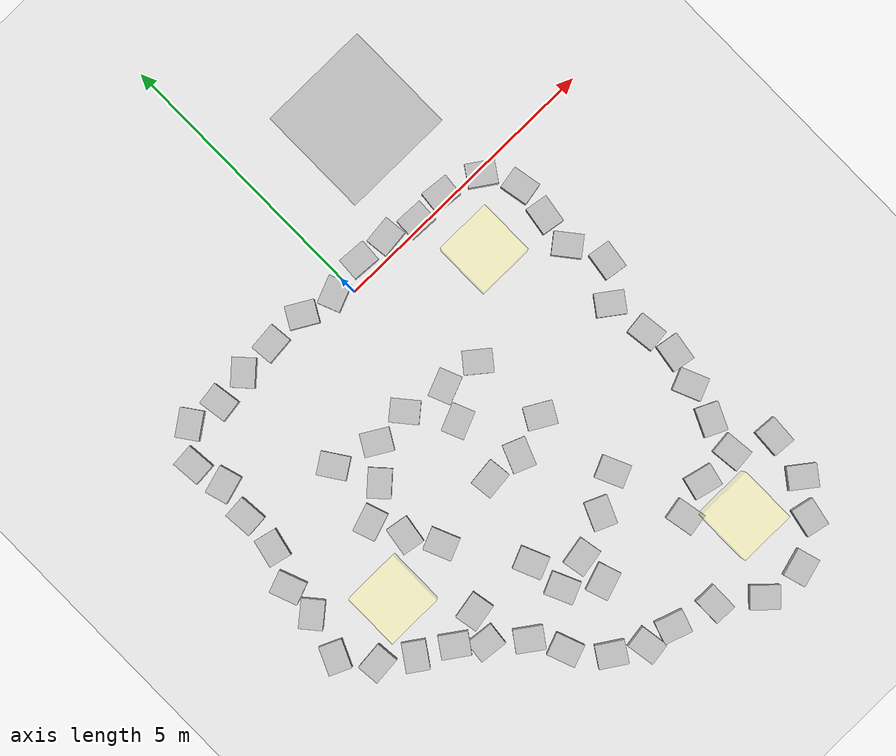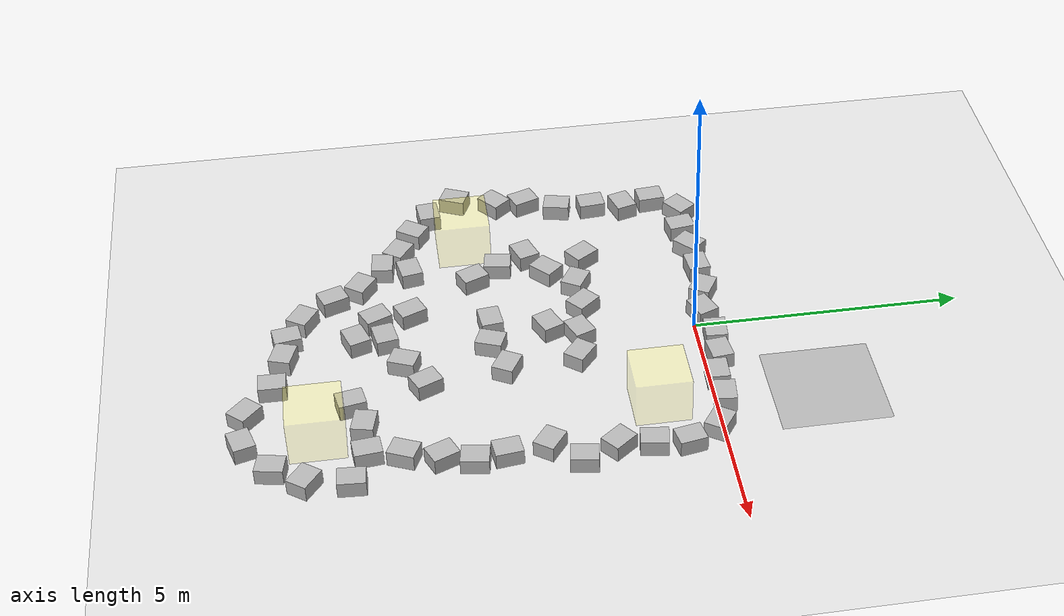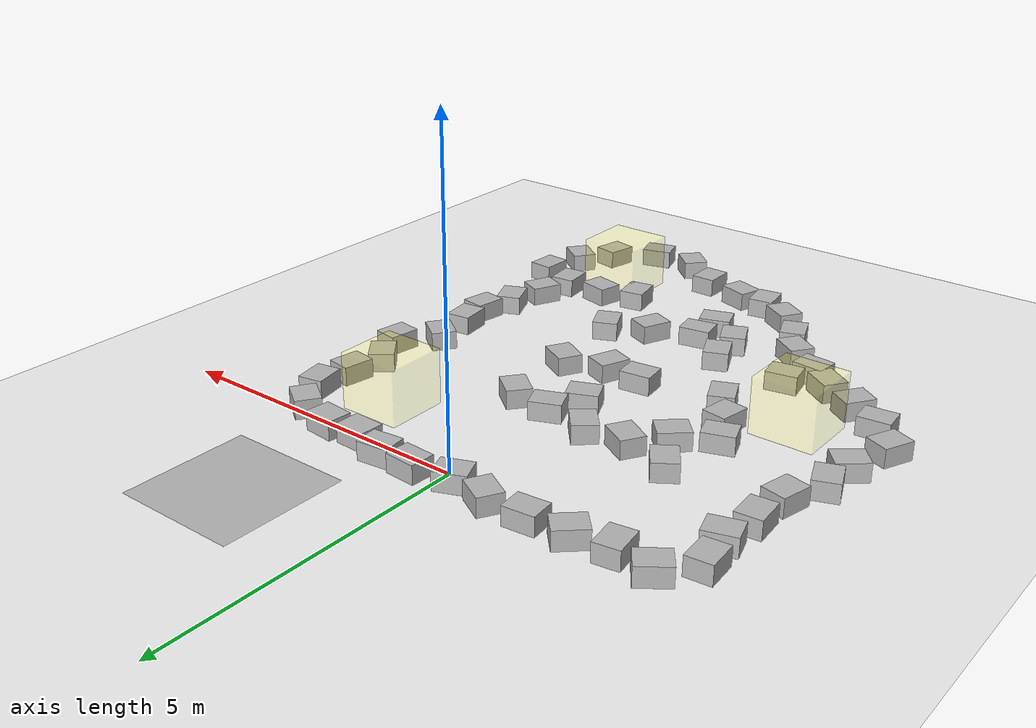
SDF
<sdf version="1.6">
 <world name="default">
  <light name="sun" type="directional">
   <pose>0 0 10 0 -0 0</pose>
   <diffuse>0.8 0.8 0.8 1</diffuse>
   <specular>0.2 0.2 0.2 1</specular>
   <attenuation>
    <range>1000</range>
    <constant>0.9</constant>
    <linear>0.01</linear>
    <quadratic>0.001</quadratic>
   </attenuation>
   <direction>-0.5 0.1 -0.9</direction>
  </light>
  <model name="ground_plane">
   <static>1</static>
   <link name="link">
    <collision name="collision">
     <geometry><plane><normal>0 0 1</normal><size>100 100</size></plane></geometry>
     <surface><friction><ode><mu>100</mu><mu2>50</mu2></ode></friction></surface>
    </collision>
    <visual name="visual">
     <cast_shadows>0</cast_shadows>
     <geometry><plane><normal>0 0 1</normal><size>100 100</size></plane></geometry>
     <material>
      <script><uri>file://media/materials/scripts/gazebo.material</uri><name>Gazebo/Grey</name></script>
     </material>
    </visual>
   </link>
  </model>
  <gravity>0 0 -9.8</gravity>
  <magnetic_field>6e-06 2.3e-05 -4.2e-05</magnetic_field>
  <atmosphere type="adiabatic"/>
  <physics name="default_physics" default="0" type="ode">
   <max_step_size>0.0008</max_step_size>
   <real_time_factor>1</real_time_factor>
   <real_time_update_rate>1250</real_time_update_rate>
   <max_contacts>5</max_contacts>
   <ode>
    <solver>
     <type>quick</type>
     <iters>10</iters>
     <sor>1.1</sor>
     <use_dynamic_moi_rescaling>0</use_dynamic_moi_rescaling>
    </solver>
    <constraints>
     <cfm>0</cfm>
     <erp>0.2</erp>
     <contact_max_correcting_vel>100</contact_max_correcting_vel>
     <contact_surface_layer>0</contact_surface_layer>
    </constraints>
   </ode>
  </physics>
  <scene><ambient>0.4 0.4 0.4 1</ambient><background>0.7 0.7 0.7 1</background><shadows>1</shadows></scene>
  <audio><device>default</device></audio>
  <spherical_coordinates>
   <surface_model>EARTH_WGS84</surface_model>
   <latitude_deg>0</latitude_deg>
   <longitude_deg>0</longitude_deg>
   <elevation>0</elevation>
   <heading_deg>0</heading_deg>
  </spherical_coordinates>
  <model name="checkerboard_plane_clone_clone">
   <static>1</static>
   <link name="link">
    <visual name="visual">
     <geometry><mesh><uri>model://checkerboard_plane/meshes/checkerboard_plane.dae</uri></mesh></geometry>
    </visual>
   </link>
   <pose>2.00075 2.00686 0.001 0 -0 0</pose>
  </model>
  <model name="RegionEventBox">
   <static>1</static>
   <pose>1.98392 -1.00365 0 0 -0 0</pose>
   <link name="link">
    <visual name="visual">
     <transparency>0.75</transparency>
     <geometry><box><size>1 1 1.75</size></box></geometry>
     <material>
      <script><uri>file://media/materials/scripts/gazebo.material</uri><name>Gazebo/Yellow</name></script>
     </material>
    </visual>
   </link>
   <plugin name="region_event_box" filename="libRegionEventBoxPlugin.so">
    <event><name>model_in_region_event_box</name><type>inclusion</type><active>1</active></event>
   </plugin>
  </model>
  <model name="RegionEventBox_0">
   <static>1</static>
   <pose>-3.01163 -4.00619 0 0 -0 0</pose>
   <link name="link">
    <visual name="visual">
     <transparency>0.75</transparency>
     <geometry><box><size>1 1 1.75</size></box></geometry>
     <material>
      <script><uri>file://media/materials/scripts/gazebo.material</uri><name>Gazebo/Yellow</name></script>
     </material>
    </visual>
   </link>
   <plugin name="region_event_box" filename="libRegionEventBoxPlugin.so">
    <event><name>model_in_region_event_box</name><type>inclusion</type><active>1</active></event>
   </plugin>
  </model>
  <model name="RegionEventBox_1">
   <static>1</static>
   <pose>1.97376 -7.01112 0 0 -0 0</pose>
   <link name="link">
    <visual name="visual">
     <transparency>0.75</transparency>
     <geometry><box><size>1 1 1.75</size></box></geometry>
     <material>
      <script><uri>file://media/materials/scripts/gazebo.material</uri><name>Gazebo/Yellow</name></script>
     </material>
    </visual>
   </link>
   <plugin name="region_event_box" filename="libRegionEventBoxPlugin.so">
    <event><name>model_in_region_event_box</name><type>inclusion</type><active>1</active></event>
   </plugin>
  </model>
  <model name="cardboard_box_clone_clone_clone_clone_0_clone_clone_clone_0_clone">
   <link name="link">
    <inertial>
     <mass>2</mass>
     <inertia>
      <ixx>0.0416667</ixx>
      <ixy>0</ixy>
      <ixz>0</ixz>
      <iyy>0.0566667</iyy>
      <iyz>0</iyz>
      <izz>0.0683333</izz>
     </inertia>
    </inertial>
    <visual name="visual">
     <pose>0 0 -0.15 0 -0 0</pose>
     <geometry>
      <mesh><uri>model://cardboard_box/meshes/cardboard_box.dae</uri><scale>1.25932 1.00745 0.755591</scale></mesh>
     </geometry>
    </visual>
    <collision name="collision">
     <geometry><box><size>0.5 0.4 0.3</size></box></geometry>
     <surface>
      <friction>
       <ode><mu>1</mu><mu2>1</mu2><fdir1>0 0 0</fdir1><slip1>0</slip1><slip2>0</slip2></ode>
       <torsional>
        <coefficient>1</coefficient>
        <patch_radius>0</patch_radius>
        <surface_radius>0</surface_radius>
        <use_patch_radius>1</use_patch_radius>
        <ode><slip>0</slip></ode>
       </torsional>
      </friction>
      <bounce><restitution_coefficient>0</restitution_coefficient><threshold>1e+06</threshold></bounce>
      <contact>
       <collide_without_contact>0</collide_without_contact>
       <collide_without_contact_bitmask>1</collide_without_contact_bitmask>
       <collide_bitmask>1</collide_bitmask>
       <ode>
        <soft_cfm>0</soft_cfm>
        <soft_erp>0.2</soft_erp>
        <kp>1e+07</kp>
        <kd>1</kd>
        <max_vel>0.1</max_vel>
        <min_depth>0.001</min_depth>
       </ode>
       <bullet>
        <split_impulse>1</split_impulse>
        <split_impulse_penetration_threshold>-0.01</split_impulse_penetration_threshold>
        <soft_cfm>0</soft_cfm>
        <soft_erp>0.2</soft_erp>
        <kp>1e+07</kp>
        <kd>1</kd>
       </bullet>
      </contact>
     </surface>
    </collision>
   </link>
   <static>1</static>
   <pose>-1.55415 0.335481 0.15 0 0 -3.04875</pose>
  </model>
  <model name="cardboard_box_clone_clone_clone_clone_0_clone_clone_clone_0_clone_0">
   <link name="link">
    <inertial>
     <mass>2</mass>
     <inertia>
      <ixx>0.0416667</ixx>
      <ixy>0</ixy>
      <ixz>0</ixz>
      <iyy>0.0566667</iyy>
      <iyz>0</iyz>
      <izz>0.0683333</izz>
     </inertia>
    </inertial>
    <visual name="visual">
     <pose>0 0 -0.15 0 -0 0</pose>
     <geometry>
      <mesh><uri>model://cardboard_box/meshes/cardboard_box.dae</uri><scale>1.25932 1.00745 0.755591</scale></mesh>
     </geometry>
    </visual>
    <collision name="collision">
     <geometry><box><size>0.5 0.4 0.3</size></box></geometry>
     <surface>
      <friction>
       <ode><mu>1</mu><mu2>1</mu2><fdir1>0 0 0</fdir1><slip1>0</slip1><slip2>0</slip2></ode>
       <torsional>
        <coefficient>1</coefficient>
        <patch_radius>0</patch_radius>
        <surface_radius>0</surface_radius>
        <use_patch_radius>1</use_patch_radius>
        <ode><slip>0</slip></ode>
       </torsional>
      </friction>
      <bounce><restitution_coefficient>0</restitution_coefficient><threshold>1e+06</threshold></bounce>
      <contact>
       <collide_without_contact>0</collide_without_contact>
       <collide_without_contact_bitmask>1</collide_without_contact_bitmask>
       <collide_bitmask>1</collide_bitmask>
       <ode>
        <soft_cfm>0</soft_cfm>
        <soft_erp>0.2</soft_erp>
        <kp>1e+07</kp>
        <kd>1</kd>
        <max_vel>0.1</max_vel>
        <min_depth>0.001</min_depth>
       </ode>
       <bullet>
        <split_impulse>1</split_impulse>
        <split_impulse_penetration_threshold>-0.01</split_impulse_penetration_threshold>
        <soft_cfm>0</soft_cfm>
        <soft_erp>0.2</soft_erp>
        <kp>1e+07</kp>
        <kd>1</kd>
       </bullet>
      </contact>
     </surface>
    </collision>
   </link>
   <static>1</static>
   <pose>-0.862628 0.321441 0.15 0 -0 2.62469</pose>
  </model>
  <model name="cardboard_box_clone_clone_clone_clone_0_clone_clone_clone_0_clone_1">
   <link name="link">
    <inertial>
     <mass>2</mass>
     <inertia>
      <ixx>0.0416667</ixx>
      <ixy>0</ixy>
      <ixz>0</ixz>
      <iyy>0.0566667</iyy>
      <iyz>0</iyz>
      <izz>0.0683333</izz>
     </inertia>
    </inertial>
    <visual name="visual">
     <pose>0 0 -0.15 0 -0 0</pose>
     <geometry>
      <mesh><uri>model://cardboard_box/meshes/cardboard_box.dae</uri><scale>1.25932 1.00745 0.755591</scale></mesh>
     </geometry>
    </visual>
    <collision name="collision">
     <geometry><box><size>0.5 0.4 0.3</size></box></geometry>
     <surface>
      <friction>
       <ode><mu>1</mu><mu2>1</mu2><fdir1>0 0 0</fdir1><slip1>0</slip1><slip2>0</slip2></ode>
       <torsional>
        <coefficient>1</coefficient>
        <patch_radius>0</patch_radius>
        <surface_radius>0</surface_radius>
        <use_patch_radius>1</use_patch_radius>
        <ode><slip>0</slip></ode>
       </torsional>
      </friction>
      <bounce><restitution_coefficient>0</restitution_coefficient><threshold>1e+06</threshold></bounce>
      <contact>
       <collide_without_contact>0</collide_without_contact>
       <collide_without_contact_bitmask>1</collide_without_contact_bitmask>
       <collide_bitmask>1</collide_bitmask>
       <ode>
        <soft_cfm>0</soft_cfm>
        <soft_erp>0.2</soft_erp>
        <kp>1e+07</kp>
        <kd>1</kd>
        <max_vel>0.1</max_vel>
        <min_depth>0.001</min_depth>
       </ode>
       <bullet>
        <split_impulse>1</split_impulse>
        <split_impulse_penetration_threshold>-0.01</split_impulse_penetration_threshold>
        <soft_cfm>0</soft_cfm>
        <soft_erp>0.2</soft_erp>
        <kp>1e+07</kp>
        <kd>1</kd>
       </bullet>
      </contact>
     </surface>
    </collision>
   </link>
   <static>1</static>
   <pose>-0.24972 0.197392 0.15 0 0 -2.75626</pose>
  </model>
  <model name="cardboard_box_clone_clone_clone_clone_0_clone_clone_clone_0_clone_2">
   <link name="link">
    <inertial>
     <mass>2</mass>
     <inertia>
      <ixx>0.0416667</ixx>
      <ixy>0</ixy>
      <ixz>0</ixz>
      <iyy>0.0566667</iyy>
      <iyz>0</iyz>
      <izz>0.0683333</izz>
     </inertia>
    </inertial>
    <visual name="visual">
     <pose>0 0 -0.15 0 -0 0</pose>
     <geometry>
      <mesh><uri>model://cardboard_box/meshes/cardboard_box.dae</uri><scale>1.25932 1.00745 0.755591</scale></mesh>
     </geometry>
    </visual>
    <collision name="collision">
     <geometry><box><size>0.5 0.4 0.3</size></box></geometry>
     <surface>
      <friction>
       <ode><mu>1</mu><mu2>1</mu2><fdir1>0 0 0</fdir1><slip1>0</slip1><slip2>0</slip2></ode>
       <torsional>
        <coefficient>1</coefficient>
        <patch_radius>0</patch_radius>
        <surface_radius>0</surface_radius>
        <use_patch_radius>1</use_patch_radius>
        <ode><slip>0</slip></ode>
       </torsional>
      </friction>
      <bounce><restitution_coefficient>0</restitution_coefficient><threshold>1e+06</threshold></bounce>
      <contact>
       <collide_without_contact>0</collide_without_contact>
       <collide_without_contact_bitmask>1</collide_without_contact_bitmask>
       <collide_bitmask>1</collide_bitmask>
       <ode>
        <soft_cfm>0</soft_cfm>
        <soft_erp>0.2</soft_erp>
        <kp>1e+07</kp>
        <kd>1</kd>
        <max_vel>0.1</max_vel>
        <min_depth>0.001</min_depth>
       </ode>
       <bullet>
        <split_impulse>1</split_impulse>
        <split_impulse_penetration_threshold>-0.01</split_impulse_penetration_threshold>
        <soft_cfm>0</soft_cfm>
        <soft_erp>0.2</soft_erp>
        <kp>1e+07</kp>
        <kd>1</kd>
       </bullet>
      </contact>
     </surface>
    </collision>
   </link>
   <static>1</static>
   <pose>0.422178 0.309321 0.15 0 -0 3.07826</pose>
  </model>
  <model name="cardboard_box_clone_clone_clone_clone_0_clone_clone_clone_0_clone_3">
   <link name="link">
    <inertial>
     <mass>2</mass>
     <inertia>
      <ixx>0.0416667</ixx>
      <ixy>0</ixy>
      <ixz>0</ixz>
      <iyy>0.0566667</iyy>
      <iyz>0</iyz>
      <izz>0.0683333</izz>
     </inertia>
    </inertial>
    <visual name="visual">
     <pose>0 0 -0.15 0 -0 0</pose>
     <geometry>
      <mesh><uri>model://cardboard_box/meshes/cardboard_box.dae</uri><scale>1.25932 1.00745 0.755591</scale></mesh>
     </geometry>
    </visual>
    <collision name="collision">
     <geometry><box><size>0.5 0.4 0.3</size></box></geometry>
     <surface>
      <friction>
       <ode><mu>1</mu><mu2>1</mu2><fdir1>0 0 0</fdir1><slip1>0</slip1><slip2>0</slip2></ode>
       <torsional>
        <coefficient>1</coefficient>
        <patch_radius>0</patch_radius>
        <surface_radius>0</surface_radius>
        <use_patch_radius>1</use_patch_radius>
        <ode><slip>0</slip></ode>
       </torsional>
      </friction>
      <bounce><restitution_coefficient>0</restitution_coefficient><threshold>1e+06</threshold></bounce>
      <contact>
       <collide_without_contact>0</collide_without_contact>
       <collide_without_contact_bitmask>1</collide_without_contact_bitmask>
       <collide_bitmask>1</collide_bitmask>
       <ode>
        <soft_cfm>0</soft_cfm>
        <soft_erp>0.2</soft_erp>
        <kp>1e+07</kp>
        <kd>1</kd>
        <max_vel>0.1</max_vel>
        <min_depth>0.001</min_depth>
       </ode>
       <bullet>
        <split_impulse>1</split_impulse>
        <split_impulse_penetration_threshold>-0.01</split_impulse_penetration_threshold>
        <soft_cfm>0</soft_cfm>
        <soft_erp>0.2</soft_erp>
        <kp>1e+07</kp>
        <kd>1</kd>
       </bullet>
      </contact>
     </surface>
    </collision>
   </link>
   <static>1</static>
   <pose>0.999361 0.271245 0.15 0 0 -3.0301</pose>
  </model>
  <model name="cardboard_box_clone_clone_clone_clone_0_clone_clone_clone_0_clone_4">
   <link name="link">
    <inertial>
     <mass>2</mass>
     <inertia>
      <ixx>0.0416667</ixx>
      <ixy>0</ixy>
      <ixz>0</ixz>
      <iyy>0.0566667</iyy>
      <iyz>0</iyz>
      <izz>0.0683333</izz>
     </inertia>
    </inertial>
    <visual name="visual">
     <pose>0 0 -0.15 0 -0 0</pose>
     <geometry>
      <mesh><uri>model://cardboard_box/meshes/cardboard_box.dae</uri><scale>1.25932 1.00745 0.755591</scale></mesh>
     </geometry>
    </visual>
    <collision name="collision">
     <geometry><box><size>0.5 0.4 0.3</size></box></geometry>
     <surface>
      <friction>
       <ode><mu>1</mu><mu2>1</mu2><fdir1>0 0 0</fdir1><slip1>0</slip1><slip2>0</slip2></ode>
       <torsional>
        <coefficient>1</coefficient>
        <patch_radius>0</patch_radius>
        <surface_radius>0</surface_radius>
        <use_patch_radius>1</use_patch_radius>
        <ode><slip>0</slip></ode>
       </torsional>
      </friction>
      <bounce><restitution_coefficient>0</restitution_coefficient><threshold>1e+06</threshold></bounce>
      <contact>
       <collide_without_contact>0</collide_without_contact>
       <collide_without_contact_bitmask>1</collide_without_contact_bitmask>
       <collide_bitmask>1</collide_bitmask>
       <ode>
        <soft_cfm>0</soft_cfm>
        <soft_erp>0.2</soft_erp>
        <kp>1e+07</kp>
        <kd>1</kd>
        <max_vel>0.1</max_vel>
        <min_depth>0.001</min_depth>
       </ode>
       <bullet>
        <split_impulse>1</split_impulse>
        <split_impulse_penetration_threshold>-0.01</split_impulse_penetration_threshold>
        <soft_cfm>0</soft_cfm>
        <soft_erp>0.2</soft_erp>
        <kp>1e+07</kp>
        <kd>1</kd>
       </bullet>
      </contact>
     </surface>
    </collision>
   </link>
   <static>1</static>
   <pose>1.54115 0.121129 0.15 0 -0 3.10477</pose>
  </model>
  <model name="cardboard_box_clone_clone_clone_clone_0_clone_clone_clone_0_clone_5">
   <link name="link">
    <inertial>
     <mass>2</mass>
     <inertia>
      <ixx>0.0416667</ixx>
      <ixy>0</ixy>
      <ixz>0</ixz>
      <iyy>0.0566667</iyy>
      <iyz>0</iyz>
      <izz>0.0683333</izz>
     </inertia>
    </inertial>
    <visual name="visual">
     <pose>0 0 -0.15 0 -0 0</pose>
     <geometry>
      <mesh><uri>model://cardboard_box/meshes/cardboard_box.dae</uri><scale>1.25932 1.00745 0.755591</scale></mesh>
     </geometry>
    </visual>
    <collision name="collision">
     <geometry><box><size>0.5 0.4 0.3</size></box></geometry>
     <surface>
      <friction>
       <ode><mu>1</mu><mu2>1</mu2><fdir1>0 0 0</fdir1><slip1>0</slip1><slip2>0</slip2></ode>
       <torsional>
        <coefficient>1</coefficient>
        <patch_radius>0</patch_radius>
        <surface_radius>0</surface_radius>
        <use_patch_radius>1</use_patch_radius>
        <ode><slip>0</slip></ode>
       </torsional>
      </friction>
      <bounce><restitution_coefficient>0</restitution_coefficient><threshold>1e+06</threshold></bounce>
      <contact>
       <collide_without_contact>0</collide_without_contact>
       <collide_without_contact_bitmask>1</collide_without_contact_bitmask>
       <collide_bitmask>1</collide_bitmask>
       <ode>
        <soft_cfm>0</soft_cfm>
        <soft_erp>0.2</soft_erp>
        <kp>1e+07</kp>
        <kd>1</kd>
        <max_vel>0.1</max_vel>
        <min_depth>0.001</min_depth>
       </ode>
       <bullet>
        <split_impulse>1</split_impulse>
        <split_impulse_penetration_threshold>-0.01</split_impulse_penetration_threshold>
        <soft_cfm>0</soft_cfm>
        <soft_erp>0.2</soft_erp>
        <kp>1e+07</kp>
        <kd>1</kd>
       </bullet>
      </contact>
     </surface>
    </collision>
   </link>
   <static>1</static>
   <pose>2.12867 0.141772 0.15 0 -0 3.044</pose>
  </model>
  <model name="cardboard_box_clone_clone_clone_clone_0_clone_clone_clone_0_clone_6">
   <link name="link">
    <inertial>
     <mass>2</mass>
     <inertia>
      <ixx>0.0416667</ixx>
      <ixy>0</ixy>
      <ixz>0</ixz>
      <iyy>0.0566667</iyy>
      <iyz>0</iyz>
      <izz>0.0683333</izz>
     </inertia>
    </inertial>
    <visual name="visual">
     <pose>0 0 -0.15 0 -0 0</pose>
     <geometry>
      <mesh><uri>model://cardboard_box/meshes/cardboard_box.dae</uri><scale>1.25932 1.00745 0.755591</scale></mesh>
     </geometry>
    </visual>
    <collision name="collision">
     <geometry><box><size>0.5 0.4 0.3</size></box></geometry>
     <surface>
      <friction>
       <ode><mu>1</mu><mu2>1</mu2><fdir1>0 0 0</fdir1><slip1>0</slip1><slip2>0</slip2></ode>
       <torsional>
        <coefficient>1</coefficient>
        <patch_radius>0</patch_radius>
        <surface_radius>0</surface_radius>
        <use_patch_radius>1</use_patch_radius>
        <ode><slip>0</slip></ode>
       </torsional>
      </friction>
      <bounce><restitution_coefficient>0</restitution_coefficient><threshold>1e+06</threshold></bounce>
      <contact>
       <collide_without_contact>0</collide_without_contact>
       <collide_without_contact_bitmask>1</collide_without_contact_bitmask>
       <collide_bitmask>1</collide_bitmask>
       <ode>
        <soft_cfm>0</soft_cfm>
        <soft_erp>0.2</soft_erp>
        <kp>1e+07</kp>
        <kd>1</kd>
        <max_vel>0.1</max_vel>
        <min_depth>0.001</min_depth>
       </ode>
       <bullet>
        <split_impulse>1</split_impulse>
        <split_impulse_penetration_threshold>-0.01</split_impulse_penetration_threshold>
        <soft_cfm>0</soft_cfm>
        <soft_erp>0.2</soft_erp>
        <kp>1e+07</kp>
        <kd>1</kd>
       </bullet>
      </contact>
     </surface>
    </collision>
   </link>
   <static>1</static>
   <pose>2.82942 -0.08159 0.15 0 -0 2.54743</pose>
  </model>
  <model name="cardboard_box_clone_clone_clone_clone_0_clone_clone_clone_0_clone_7">
   <link name="link">
    <inertial>
     <mass>2</mass>
     <inertia>
      <ixx>0.0416667</ixx>
      <ixy>0</ixy>
      <ixz>0</ixz>
      <iyy>0.0566667</iyy>
      <iyz>0</iyz>
      <izz>0.0683333</izz>
     </inertia>
    </inertial>
    <visual name="visual">
     <pose>0 0 -0.15 0 -0 0</pose>
     <geometry>
      <mesh><uri>model://cardboard_box/meshes/cardboard_box.dae</uri><scale>1.25932 1.00745 0.755591</scale></mesh>
     </geometry>
    </visual>
    <collision name="collision">
     <geometry><box><size>0.5 0.4 0.3</size></box></geometry>
     <surface>
      <friction>
       <ode><mu>1</mu><mu2>1</mu2><fdir1>0 0 0</fdir1><slip1>0</slip1><slip2>0</slip2></ode>
       <torsional>
        <coefficient>1</coefficient>
        <patch_radius>0</patch_radius>
        <surface_radius>0</surface_radius>
        <use_patch_radius>1</use_patch_radius>
        <ode><slip>0</slip></ode>
       </torsional>
      </friction>
      <bounce><restitution_coefficient>0</restitution_coefficient><threshold>1e+06</threshold></bounce>
      <contact>
       <collide_without_contact>0</collide_without_contact>
       <collide_without_contact_bitmask>1</collide_without_contact_bitmask>
       <collide_bitmask>1</collide_bitmask>
       <ode>
        <soft_cfm>0</soft_cfm>
        <soft_erp>0.2</soft_erp>
        <kp>1e+07</kp>
        <kd>1</kd>
        <max_vel>0.1</max_vel>
        <min_depth>0.001</min_depth>
       </ode>
       <bullet>
        <split_impulse>1</split_impulse>
        <split_impulse_penetration_threshold>-0.01</split_impulse_penetration_threshold>
        <soft_cfm>0</soft_cfm>
        <soft_erp>0.2</soft_erp>
        <kp>1e+07</kp>
        <kd>1</kd>
       </bullet>
      </contact>
     </surface>
    </collision>
   </link>
   <static>1</static>
   <pose>3.14465 -0.664614 0.15 0 -0 1.75678</pose>
  </model>
  <model name="cardboard_box_clone_clone_clone_clone_0_clone_clone_clone_0_clone_8">
   <link name="link">
    <inertial>
     <mass>2</mass>
     <inertia>
      <ixx>0.0416667</ixx>
      <ixy>0</ixy>
      <ixz>0</ixz>
      <iyy>0.0566667</iyy>
      <iyz>0</iyz>
      <izz>0.0683333</izz>
     </inertia>
    </inertial>
    <visual name="visual">
     <pose>0 0 -0.15 0 -0 0</pose>
     <geometry>
      <mesh><uri>model://cardboard_box/meshes/cardboard_box.dae</uri><scale>1.25932 1.00745 0.755591</scale></mesh>
     </geometry>
    </visual>
    <collision name="collision">
     <geometry><box><size>0.5 0.4 0.3</size></box></geometry>
     <surface>
      <friction>
       <ode><mu>1</mu><mu2>1</mu2><fdir1>0 0 0</fdir1><slip1>0</slip1><slip2>0</slip2></ode>
       <torsional>
        <coefficient>1</coefficient>
        <patch_radius>0</patch_radius>
        <surface_radius>0</surface_radius>
        <use_patch_radius>1</use_patch_radius>
        <ode><slip>0</slip></ode>
       </torsional>
      </friction>
      <bounce><restitution_coefficient>0</restitution_coefficient><threshold>1e+06</threshold></bounce>
      <contact>
       <collide_without_contact>0</collide_without_contact>
       <collide_without_contact_bitmask>1</collide_without_contact_bitmask>
       <collide_bitmask>1</collide_bitmask>
       <ode>
        <soft_cfm>0</soft_cfm>
        <soft_erp>0.2</soft_erp>
        <kp>1e+07</kp>
        <kd>1</kd>
        <max_vel>0.1</max_vel>
        <min_depth>0.001</min_depth>
       </ode>
       <bullet>
        <split_impulse>1</split_impulse>
        <split_impulse_penetration_threshold>-0.01</split_impulse_penetration_threshold>
        <soft_cfm>0</soft_cfm>
        <soft_erp>0.2</soft_erp>
        <kp>1e+07</kp>
        <kd>1</kd>
       </bullet>
      </contact>
     </surface>
    </collision>
   </link>
   <static>1</static>
   <pose>3.0944 -1.28365 0.15 0 -0 1.41338</pose>
  </model>
  <model name="cardboard_box_clone_clone_clone_clone_0_clone_clone_clone_0_clone_9">
   <link name="link">
    <inertial>
     <mass>2</mass>
     <inertia>
      <ixx>0.0416667</ixx>
      <ixy>0</ixy>
      <ixz>0</ixz>
      <iyy>0.0566667</iyy>
      <iyz>0</iyz>
      <izz>0.0683333</izz>
     </inertia>
    </inertial>
    <visual name="visual">
     <pose>0 0 -0.15 0 -0 0</pose>
     <geometry>
      <mesh><uri>model://cardboard_box/meshes/cardboard_box.dae</uri><scale>1.25932 1.00745 0.755591</scale></mesh>
     </geometry>
    </visual>
    <collision name="collision">
     <geometry><box><size>0.5 0.4 0.3</size></box></geometry>
     <surface>
      <friction>
       <ode><mu>1</mu><mu2>1</mu2><fdir1>0 0 0</fdir1><slip1>0</slip1><slip2>0</slip2></ode>
       <torsional>
        <coefficient>1</coefficient>
        <patch_radius>0</patch_radius>
        <surface_radius>0</surface_radius>
        <use_patch_radius>1</use_patch_radius>
        <ode><slip>0</slip></ode>
       </torsional>
      </friction>
      <bounce><restitution_coefficient>0</restitution_coefficient><threshold>1e+06</threshold></bounce>
      <contact>
       <collide_without_contact>0</collide_without_contact>
       <collide_without_contact_bitmask>1</collide_without_contact_bitmask>
       <collide_bitmask>1</collide_bitmask>
       <ode>
        <soft_cfm>0</soft_cfm>
        <soft_erp>0.2</soft_erp>
        <kp>1e+07</kp>
        <kd>1</kd>
        <max_vel>0.1</max_vel>
        <min_depth>0.001</min_depth>
       </ode>
       <bullet>
        <split_impulse>1</split_impulse>
        <split_impulse_penetration_threshold>-0.01</split_impulse_penetration_threshold>
        <soft_cfm>0</soft_cfm>
        <soft_erp>0.2</soft_erp>
        <kp>1e+07</kp>
        <kd>1</kd>
       </bullet>
      </contact>
     </surface>
    </collision>
   </link>
   <static>1</static>
   <pose>3.02239 -1.89125 0.15 0 -0 2.24391</pose>
  </model>
  <model name="cardboard_box_clone_clone_clone_clone_0_clone_clone_clone_0_clone_10">
   <link name="link">
    <inertial>
     <mass>2</mass>
     <inertia>
      <ixx>0.0416667</ixx>
      <ixy>0</ixy>
      <ixz>0</ixz>
      <iyy>0.0566667</iyy>
      <iyz>0</iyz>
      <izz>0.0683333</izz>
     </inertia>
    </inertial>
    <visual name="visual">
     <pose>0 0 -0.15 0 -0 0</pose>
     <geometry>
      <mesh><uri>model://cardboard_box/meshes/cardboard_box.dae</uri><scale>1.25932 1.00745 0.755591</scale></mesh>
     </geometry>
    </visual>
    <collision name="collision">
     <geometry><box><size>0.5 0.4 0.3</size></box></geometry>
     <surface>
      <friction>
       <ode><mu>1</mu><mu2>1</mu2><fdir1>0 0 0</fdir1><slip1>0</slip1><slip2>0</slip2></ode>
       <torsional>
        <coefficient>1</coefficient>
        <patch_radius>0</patch_radius>
        <surface_radius>0</surface_radius>
        <use_patch_radius>1</use_patch_radius>
        <ode><slip>0</slip></ode>
       </torsional>
      </friction>
      <bounce><restitution_coefficient>0</restitution_coefficient><threshold>1e+06</threshold></bounce>
      <contact>
       <collide_without_contact>0</collide_without_contact>
       <collide_without_contact_bitmask>1</collide_without_contact_bitmask>
       <collide_bitmask>1</collide_bitmask>
       <ode>
        <soft_cfm>0</soft_cfm>
        <soft_erp>0.2</soft_erp>
        <kp>1e+07</kp>
        <kd>1</kd>
        <max_vel>0.1</max_vel>
        <min_depth>0.001</min_depth>
       </ode>
       <bullet>
        <split_impulse>1</split_impulse>
        <split_impulse_penetration_threshold>-0.01</split_impulse_penetration_threshold>
        <soft_cfm>0</soft_cfm>
        <soft_erp>0.2</soft_erp>
        <kp>1e+07</kp>
        <kd>1</kd>
       </bullet>
      </contact>
     </surface>
    </collision>
   </link>
   <static>1</static>
   <pose>3.30498 -2.5257 0.15 0 -0 1.4221</pose>
  </model>
  <model name="cardboard_box_clone_clone_clone_clone_0_clone_clone_clone_0_clone_11">
   <link name="link">
    <inertial>
     <mass>2</mass>
     <inertia>
      <ixx>0.0416667</ixx>
      <ixy>0</ixy>
      <ixz>0</ixz>
      <iyy>0.0566667</iyy>
      <iyz>0</iyz>
      <izz>0.0683333</izz>
     </inertia>
    </inertial>
    <visual name="visual">
     <pose>0 0 -0.15 0 -0 0</pose>
     <geometry>
      <mesh><uri>model://cardboard_box/meshes/cardboard_box.dae</uri><scale>1.25932 1.00745 0.755591</scale></mesh>
     </geometry>
    </visual>
    <collision name="collision">
     <geometry><box><size>0.5 0.4 0.3</size></box></geometry>
     <surface>
      <friction>
       <ode><mu>1</mu><mu2>1</mu2><fdir1>0 0 0</fdir1><slip1>0</slip1><slip2>0</slip2></ode>
       <torsional>
        <coefficient>1</coefficient>
        <patch_radius>0</patch_radius>
        <surface_radius>0</surface_radius>
        <use_patch_radius>1</use_patch_radius>
        <ode><slip>0</slip></ode>
       </torsional>
      </friction>
      <bounce><restitution_coefficient>0</restitution_coefficient><threshold>1e+06</threshold></bounce>
      <contact>
       <collide_without_contact>0</collide_without_contact>
       <collide_without_contact_bitmask>1</collide_without_contact_bitmask>
       <collide_bitmask>1</collide_bitmask>
       <ode>
        <soft_cfm>0</soft_cfm>
        <soft_erp>0.2</soft_erp>
        <kp>1e+07</kp>
        <kd>1</kd>
        <max_vel>0.1</max_vel>
        <min_depth>0.001</min_depth>
       </ode>
       <bullet>
        <split_impulse>1</split_impulse>
        <split_impulse_penetration_threshold>-0.01</split_impulse_penetration_threshold>
        <soft_cfm>0</soft_cfm>
        <soft_erp>0.2</soft_erp>
        <kp>1e+07</kp>
        <kd>1</kd>
       </bullet>
      </contact>
     </surface>
    </collision>
   </link>
   <static>1</static>
   <pose>2.8473 -3.0614 0.15 0 0 -0.629941</pose>
  </model>
  <model name="cardboard_box_clone_clone_clone_clone_0_clone_clone_clone_0_clone_11_clone_clone">
   <link name="link">
    <inertial>
     <mass>2</mass>
     <inertia>
      <ixx>0.0416667</ixx>
      <ixy>0</ixy>
      <ixz>0</ixz>
      <iyy>0.0566667</iyy>
      <iyz>0</iyz>
      <izz>0.0683333</izz>
     </inertia>
    </inertial>
    <visual name="visual">
     <pose>0 0 -0.15 0 -0 0</pose>
     <geometry>
      <mesh><uri>model://cardboard_box/meshes/cardboard_box.dae</uri><scale>1.25932 1.00745 0.755591</scale></mesh>
     </geometry>
    </visual>
    <collision name="collision">
     <geometry><box><size>0.5 0.4 0.3</size></box></geometry>
     <surface>
      <friction>
       <ode><mu>1</mu><mu2>1</mu2><fdir1>0 0 0</fdir1><slip1>0</slip1><slip2>0</slip2></ode>
       <torsional>
        <coefficient>1</coefficient>
        <patch_radius>0</patch_radius>
        <surface_radius>0</surface_radius>
        <use_patch_radius>1</use_patch_radius>
        <ode><slip>0</slip></ode>
       </torsional>
      </friction>
      <bounce><restitution_coefficient>0</restitution_coefficient><threshold>1e+06</threshold></bounce>
      <contact>
       <collide_without_contact>0</collide_without_contact>
       <collide_without_contact_bitmask>1</collide_without_contact_bitmask>
       <collide_bitmask>1</collide_bitmask>
       <ode>
        <soft_cfm>0</soft_cfm>
        <soft_erp>0.2</soft_erp>
        <kp>1e+07</kp>
        <kd>1</kd>
        <max_vel>0.1</max_vel>
        <min_depth>0.001</min_depth>
       </ode>
       <bullet>
        <split_impulse>1</split_impulse>
        <split_impulse_penetration_threshold>-0.01</split_impulse_penetration_threshold>
        <soft_cfm>0</soft_cfm>
        <soft_erp>0.2</soft_erp>
        <kp>1e+07</kp>
        <kd>1</kd>
       </bullet>
      </contact>
     </surface>
    </collision>
   </link>
   <static>1</static>
   <pose>2.94828 -3.80625 0.15 0 0 -1.45029</pose>
  </model>
  <model name="cardboard_box_clone_clone_clone_clone_0_clone_clone_clone_0_clone_11_clone_clone_0">
   <link name="link">
    <inertial>
     <mass>2</mass>
     <inertia>
      <ixx>0.0416667</ixx>
      <ixy>0</ixy>
      <ixz>0</ixz>
      <iyy>0.0566667</iyy>
      <iyz>0</iyz>
      <izz>0.0683333</izz>
     </inertia>
    </inertial>
    <visual name="visual">
     <pose>0 0 -0.15 0 -0 0</pose>
     <geometry>
      <mesh><uri>model://cardboard_box/meshes/cardboard_box.dae</uri><scale>1.25932 1.00745 0.755591</scale></mesh>
     </geometry>
    </visual>
    <collision name="collision">
     <geometry><box><size>0.5 0.4 0.3</size></box></geometry>
     <surface>
      <friction>
       <ode><mu>1</mu><mu2>1</mu2><fdir1>0 0 0</fdir1><slip1>0</slip1><slip2>0</slip2></ode>
       <torsional>
        <coefficient>1</coefficient>
        <patch_radius>0</patch_radius>
        <surface_radius>0</surface_radius>
        <use_patch_radius>1</use_patch_radius>
        <ode><slip>0</slip></ode>
       </torsional>
      </friction>
      <bounce><restitution_coefficient>0</restitution_coefficient><threshold>1e+06</threshold></bounce>
      <contact>
       <collide_without_contact>0</collide_without_contact>
       <collide_without_contact_bitmask>1</collide_without_contact_bitmask>
       <collide_bitmask>1</collide_bitmask>
       <ode>
        <soft_cfm>0</soft_cfm>
        <soft_erp>0.2</soft_erp>
        <kp>1e+07</kp>
        <kd>1</kd>
        <max_vel>0.1</max_vel>
        <min_depth>0.001</min_depth>
       </ode>
       <bullet>
        <split_impulse>1</split_impulse>
        <split_impulse_penetration_threshold>-0.01</split_impulse_penetration_threshold>
        <soft_cfm>0</soft_cfm>
        <soft_erp>0.2</soft_erp>
        <kp>1e+07</kp>
        <kd>1</kd>
       </bullet>
      </contact>
     </surface>
    </collision>
   </link>
   <static>1</static>
   <pose>3.04439 -4.36758 0.15 0 0 -1.73089</pose>
  </model>
  <model name="cardboard_box_clone_clone_clone_clone_0_clone_clone_clone_0_clone_11_clone_clone_1">
   <link name="link">
    <inertial>
     <mass>2</mass>
     <inertia>
      <ixx>0.0416667</ixx>
      <ixy>0</ixy>
      <ixz>0</ixz>
      <iyy>0.0566667</iyy>
      <iyz>0</iyz>
      <izz>0.0683333</izz>
     </inertia>
    </inertial>
    <visual name="visual">
     <pose>0 0 -0.15 0 -0 0</pose>
     <geometry>
      <mesh><uri>model://cardboard_box/meshes/cardboard_box.dae</uri><scale>1.25932 1.00745 0.755591</scale></mesh>
     </geometry>
    </visual>
    <collision name="collision">
     <geometry><box><size>0.5 0.4 0.3</size></box></geometry>
     <surface>
      <friction>
       <ode><mu>1</mu><mu2>1</mu2><fdir1>0 0 0</fdir1><slip1>0</slip1><slip2>0</slip2></ode>
       <torsional>
        <coefficient>1</coefficient>
        <patch_radius>0</patch_radius>
        <surface_radius>0</surface_radius>
        <use_patch_radius>1</use_patch_radius>
        <ode><slip>0</slip></ode>
       </torsional>
      </friction>
      <bounce><restitution_coefficient>0</restitution_coefficient><threshold>1e+06</threshold></bounce>
      <contact>
       <collide_without_contact>0</collide_without_contact>
       <collide_without_contact_bitmask>1</collide_without_contact_bitmask>
       <collide_bitmask>1</collide_bitmask>
       <ode>
        <soft_cfm>0</soft_cfm>
        <soft_erp>0.2</soft_erp>
        <kp>1e+07</kp>
        <kd>1</kd>
        <max_vel>0.1</max_vel>
        <min_depth>0.001</min_depth>
       </ode>
       <bullet>
        <split_impulse>1</split_impulse>
        <split_impulse_penetration_threshold>-0.01</split_impulse_penetration_threshold>
        <soft_cfm>0</soft_cfm>
        <soft_erp>0.2</soft_erp>
        <kp>1e+07</kp>
        <kd>1</kd>
       </bullet>
      </contact>
     </surface>
    </collision>
   </link>
   <static>1</static>
   <pose>2.86346 -4.91531 0.15 0 0 -1.16671</pose>
  </model>
  <model name="cardboard_box_clone_clone_clone_clone_0_clone_clone_clone_0_clone_11_clone_clone_2">
   <link name="link">
    <inertial>
     <mass>2</mass>
     <inertia>
      <ixx>0.0416667</ixx>
      <ixy>0</ixy>
      <ixz>0</ixz>
      <iyy>0.0566667</iyy>
      <iyz>0</iyz>
      <izz>0.0683333</izz>
     </inertia>
    </inertial>
    <visual name="visual">
     <pose>0 0 -0.15 0 -0 0</pose>
     <geometry>
      <mesh><uri>model://cardboard_box/meshes/cardboard_box.dae</uri><scale>1.25932 1.00745 0.755591</scale></mesh>
     </geometry>
    </visual>
    <collision name="collision">
     <geometry><box><size>0.5 0.4 0.3</size></box></geometry>
     <surface>
      <friction>
       <ode><mu>1</mu><mu2>1</mu2><fdir1>0 0 0</fdir1><slip1>0</slip1><slip2>0</slip2></ode>
       <torsional>
        <coefficient>1</coefficient>
        <patch_radius>0</patch_radius>
        <surface_radius>0</surface_radius>
        <use_patch_radius>1</use_patch_radius>
        <ode><slip>0</slip></ode>
       </torsional>
      </friction>
      <bounce><restitution_coefficient>0</restitution_coefficient><threshold>1e+06</threshold></bounce>
      <contact>
       <collide_without_contact>0</collide_without_contact>
       <collide_without_contact_bitmask>1</collide_without_contact_bitmask>
       <collide_bitmask>1</collide_bitmask>
       <ode>
        <soft_cfm>0</soft_cfm>
        <soft_erp>0.2</soft_erp>
        <kp>1e+07</kp>
        <kd>1</kd>
        <max_vel>0.1</max_vel>
        <min_depth>0.001</min_depth>
       </ode>
       <bullet>
        <split_impulse>1</split_impulse>
        <split_impulse_penetration_threshold>-0.01</split_impulse_penetration_threshold>
        <soft_cfm>0</soft_cfm>
        <soft_erp>0.2</soft_erp>
        <kp>1e+07</kp>
        <kd>1</kd>
       </bullet>
      </contact>
     </surface>
    </collision>
   </link>
   <static>1</static>
   <pose>2.70284 -5.55434 0.15 0 0 -2.00417</pose>
  </model>
  <model name="cardboard_box_clone_clone_clone_clone_0_clone_clone_clone_0_clone_11_clone_clone_3">
   <link name="link">
    <inertial>
     <mass>2</mass>
     <inertia>
      <ixx>0.0416667</ixx>
      <ixy>0</ixy>
      <ixz>0</ixz>
      <iyy>0.0566667</iyy>
      <iyz>0</iyz>
      <izz>0.0683333</izz>
     </inertia>
    </inertial>
    <visual name="visual">
     <pose>0 0 -0.15 0 -0 0</pose>
     <geometry>
      <mesh><uri>model://cardboard_box/meshes/cardboard_box.dae</uri><scale>1.25932 1.00745 0.755591</scale></mesh>
     </geometry>
    </visual>
    <collision name="collision">
     <geometry><box><size>0.5 0.4 0.3</size></box></geometry>
     <surface>
      <friction>
       <ode><mu>1</mu><mu2>1</mu2><fdir1>0 0 0</fdir1><slip1>0</slip1><slip2>0</slip2></ode>
       <torsional>
        <coefficient>1</coefficient>
        <patch_radius>0</patch_radius>
        <surface_radius>0</surface_radius>
        <use_patch_radius>1</use_patch_radius>
        <ode><slip>0</slip></ode>
       </torsional>
      </friction>
      <bounce><restitution_coefficient>0</restitution_coefficient><threshold>1e+06</threshold></bounce>
      <contact>
       <collide_without_contact>0</collide_without_contact>
       <collide_without_contact_bitmask>1</collide_without_contact_bitmask>
       <collide_bitmask>1</collide_bitmask>
       <ode>
        <soft_cfm>0</soft_cfm>
        <soft_erp>0.2</soft_erp>
        <kp>1e+07</kp>
        <kd>1</kd>
        <max_vel>0.1</max_vel>
        <min_depth>0.001</min_depth>
       </ode>
       <bullet>
        <split_impulse>1</split_impulse>
        <split_impulse_penetration_threshold>-0.01</split_impulse_penetration_threshold>
        <soft_cfm>0</soft_cfm>
        <soft_erp>0.2</soft_erp>
        <kp>1e+07</kp>
        <kd>1</kd>
       </bullet>
      </contact>
     </surface>
    </collision>
   </link>
   <static>1</static>
   <pose>2.57627 -6.17267 0.15 0 0 -1.46657</pose>
  </model>
  <model name="cardboard_box_clone_clone_clone_clone_0_clone_clone_clone_0_clone_11_clone_clone_4">
   <link name="link">
    <inertial>
     <mass>2</mass>
     <inertia>
      <ixx>0.0416667</ixx>
      <ixy>0</ixy>
      <ixz>0</ixz>
      <iyy>0.0566667</iyy>
      <iyz>0</iyz>
      <izz>0.0683333</izz>
     </inertia>
    </inertial>
    <visual name="visual">
     <pose>0 0 -0.15 0 -0 0</pose>
     <geometry>
      <mesh><uri>model://cardboard_box/meshes/cardboard_box.dae</uri><scale>1.25932 1.00745 0.755591</scale></mesh>
     </geometry>
    </visual>
    <collision name="collision">
     <geometry><box><size>0.5 0.4 0.3</size></box></geometry>
     <surface>
      <friction>
       <ode><mu>1</mu><mu2>1</mu2><fdir1>0 0 0</fdir1><slip1>0</slip1><slip2>0</slip2></ode>
       <torsional>
        <coefficient>1</coefficient>
        <patch_radius>0</patch_radius>
        <surface_radius>0</surface_radius>
        <use_patch_radius>1</use_patch_radius>
        <ode><slip>0</slip></ode>
       </torsional>
      </friction>
      <bounce><restitution_coefficient>0</restitution_coefficient><threshold>1e+06</threshold></bounce>
      <contact>
       <collide_without_contact>0</collide_without_contact>
       <collide_without_contact_bitmask>1</collide_without_contact_bitmask>
       <collide_bitmask>1</collide_bitmask>
       <ode>
        <soft_cfm>0</soft_cfm>
        <soft_erp>0.2</soft_erp>
        <kp>1e+07</kp>
        <kd>1</kd>
        <max_vel>0.1</max_vel>
        <min_depth>0.001</min_depth>
       </ode>
       <bullet>
        <split_impulse>1</split_impulse>
        <split_impulse_penetration_threshold>-0.01</split_impulse_penetration_threshold>
        <soft_cfm>0</soft_cfm>
        <soft_erp>0.2</soft_erp>
        <kp>1e+07</kp>
        <kd>1</kd>
       </bullet>
      </contact>
     </surface>
    </collision>
   </link>
   <static>1</static>
   <pose>3.24318 -6.47147 0.15 0 0 -1.63291</pose>
  </model>
  <model name="cardboard_box_clone_clone_clone_clone_0_clone_clone_clone_0_clone_11_clone_clone_5">
   <link name="link">
    <inertial>
     <mass>2</mass>
     <inertia>
      <ixx>0.0416667</ixx>
      <ixy>0</ixy>
      <ixz>0</ixz>
      <iyy>0.0566667</iyy>
      <iyz>0</iyz>
      <izz>0.0683333</izz>
     </inertia>
    </inertial>
    <visual name="visual">
     <pose>0 0 -0.15 0 -0 0</pose>
     <geometry>
      <mesh><uri>model://cardboard_box/meshes/cardboard_box.dae</uri><scale>1.25932 1.00745 0.755591</scale></mesh>
     </geometry>
    </visual>
    <collision name="collision">
     <geometry><box><size>0.5 0.4 0.3</size></box></geometry>
     <surface>
      <friction>
       <ode><mu>1</mu><mu2>1</mu2><fdir1>0 0 0</fdir1><slip1>0</slip1><slip2>0</slip2></ode>
       <torsional>
        <coefficient>1</coefficient>
        <patch_radius>0</patch_radius>
        <surface_radius>0</surface_radius>
        <use_patch_radius>1</use_patch_radius>
        <ode><slip>0</slip></ode>
       </torsional>
      </friction>
      <bounce><restitution_coefficient>0</restitution_coefficient><threshold>1e+06</threshold></bounce>
      <contact>
       <collide_without_contact>0</collide_without_contact>
       <collide_without_contact_bitmask>1</collide_without_contact_bitmask>
       <collide_bitmask>1</collide_bitmask>
       <ode>
        <soft_cfm>0</soft_cfm>
        <soft_erp>0.2</soft_erp>
        <kp>1e+07</kp>
        <kd>1</kd>
        <max_vel>0.1</max_vel>
        <min_depth>0.001</min_depth>
       </ode>
       <bullet>
        <split_impulse>1</split_impulse>
        <split_impulse_penetration_threshold>-0.01</split_impulse_penetration_threshold>
        <soft_cfm>0</soft_cfm>
        <soft_erp>0.2</soft_erp>
        <kp>1e+07</kp>
        <kd>1</kd>
       </bullet>
      </contact>
     </surface>
    </collision>
   </link>
   <static>1</static>
   <pose>3.11203 -7.2599 0.15 0 0 -0.644199</pose>
  </model>
  <model name="cardboard_box_clone_clone_clone_clone_0_clone_clone_clone_0_clone_11_clone_clone_6">
   <link name="link">
    <inertial>
     <mass>2</mass>
     <inertia>
      <ixx>0.0416667</ixx>
      <ixy>0</ixy>
      <ixz>0</ixz>
      <iyy>0.0566667</iyy>
      <iyz>0</iyz>
      <izz>0.0683333</izz>
     </inertia>
    </inertial>
    <visual name="visual">
     <pose>0 0 -0.15 0 -0 0</pose>
     <geometry>
      <mesh><uri>model://cardboard_box/meshes/cardboard_box.dae</uri><scale>1.25932 1.00745 0.755591</scale></mesh>
     </geometry>
    </visual>
    <collision name="collision">
     <geometry><box><size>0.5 0.4 0.3</size></box></geometry>
     <surface>
      <friction>
       <ode><mu>1</mu><mu2>1</mu2><fdir1>0 0 0</fdir1><slip1>0</slip1><slip2>0</slip2></ode>
       <torsional>
        <coefficient>1</coefficient>
        <patch_radius>0</patch_radius>
        <surface_radius>0</surface_radius>
        <use_patch_radius>1</use_patch_radius>
        <ode><slip>0</slip></ode>
       </torsional>
      </friction>
      <bounce><restitution_coefficient>0</restitution_coefficient><threshold>1e+06</threshold></bounce>
      <contact>
       <collide_without_contact>0</collide_without_contact>
       <collide_without_contact_bitmask>1</collide_without_contact_bitmask>
       <collide_bitmask>1</collide_bitmask>
       <ode>
        <soft_cfm>0</soft_cfm>
        <soft_erp>0.2</soft_erp>
        <kp>1e+07</kp>
        <kd>1</kd>
        <max_vel>0.1</max_vel>
        <min_depth>0.001</min_depth>
       </ode>
       <bullet>
        <split_impulse>1</split_impulse>
        <split_impulse_penetration_threshold>-0.01</split_impulse_penetration_threshold>
        <soft_cfm>0</soft_cfm>
        <soft_erp>0.2</soft_erp>
        <kp>1e+07</kp>
        <kd>1</kd>
       </bullet>
      </contact>
     </surface>
    </collision>
   </link>
   <static>1</static>
   <pose>2.73076 -7.81332 0.15 0 0 -1.77717</pose>
  </model>
  <model name="cardboard_box_clone_clone_clone_clone_0_clone_clone_clone_0_clone_11_clone_clone_7">
   <link name="link">
    <inertial>
     <mass>2</mass>
     <inertia>
      <ixx>0.0416667</ixx>
      <ixy>0</ixy>
      <ixz>0</ixz>
      <iyy>0.0566667</iyy>
      <iyz>0</iyz>
      <izz>0.0683333</izz>
     </inertia>
    </inertial>
    <visual name="visual">
     <pose>0 0 -0.15 0 -0 0</pose>
     <geometry>
      <mesh><uri>model://cardboard_box/meshes/cardboard_box.dae</uri><scale>1.25932 1.00745 0.755591</scale></mesh>
     </geometry>
    </visual>
    <collision name="collision">
     <geometry><box><size>0.5 0.4 0.3</size></box></geometry>
     <surface>
      <friction>
       <ode><mu>1</mu><mu2>1</mu2><fdir1>0 0 0</fdir1><slip1>0</slip1><slip2>0</slip2></ode>
       <torsional>
        <coefficient>1</coefficient>
        <patch_radius>0</patch_radius>
        <surface_radius>0</surface_radius>
        <use_patch_radius>1</use_patch_radius>
        <ode><slip>0</slip></ode>
       </torsional>
      </friction>
      <bounce><restitution_coefficient>0</restitution_coefficient><threshold>1e+06</threshold></bounce>
      <contact>
       <collide_without_contact>0</collide_without_contact>
       <collide_without_contact_bitmask>1</collide_without_contact_bitmask>
       <collide_bitmask>1</collide_bitmask>
       <ode>
        <soft_cfm>0</soft_cfm>
        <soft_erp>0.2</soft_erp>
        <kp>1e+07</kp>
        <kd>1</kd>
        <max_vel>0.1</max_vel>
        <min_depth>0.001</min_depth>
       </ode>
       <bullet>
        <split_impulse>1</split_impulse>
        <split_impulse_penetration_threshold>-0.01</split_impulse_penetration_threshold>
        <soft_cfm>0</soft_cfm>
        <soft_erp>0.2</soft_erp>
        <kp>1e+07</kp>
        <kd>1</kd>
       </bullet>
      </contact>
     </surface>
    </collision>
   </link>
   <static>1</static>
   <pose>2.06145 -8.2994 0.15 0 0 -2.86092</pose>
  </model>
  <model name="cardboard_box_clone_clone_clone_clone_0_clone_clone_clone_0_clone_11_clone_clone_8">
   <link name="link">
    <inertial>
     <mass>2</mass>
     <inertia>
      <ixx>0.0416667</ixx>
      <ixy>0</ixy>
      <ixz>0</ixz>
      <iyy>0.0566667</iyy>
      <iyz>0</iyz>
      <izz>0.0683333</izz>
     </inertia>
    </inertial>
    <visual name="visual">
     <pose>0 0 -0.15 0 -0 0</pose>
     <geometry>
      <mesh><uri>model://cardboard_box/meshes/cardboard_box.dae</uri><scale>1.25932 1.00745 0.755591</scale></mesh>
     </geometry>
    </visual>
    <collision name="collision">
     <geometry><box><size>0.5 0.4 0.3</size></box></geometry>
     <surface>
      <friction>
       <ode><mu>1</mu><mu2>1</mu2><fdir1>0 0 0</fdir1><slip1>0</slip1><slip2>0</slip2></ode>
       <torsional>
        <coefficient>1</coefficient>
        <patch_radius>0</patch_radius>
        <surface_radius>0</surface_radius>
        <use_patch_radius>1</use_patch_radius>
        <ode><slip>0</slip></ode>
       </torsional>
      </friction>
      <bounce><restitution_coefficient>0</restitution_coefficient><threshold>1e+06</threshold></bounce>
      <contact>
       <collide_without_contact>0</collide_without_contact>
       <collide_without_contact_bitmask>1</collide_without_contact_bitmask>
       <collide_bitmask>1</collide_bitmask>
       <ode>
        <soft_cfm>0</soft_cfm>
        <soft_erp>0.2</soft_erp>
        <kp>1e+07</kp>
        <kd>1</kd>
        <max_vel>0.1</max_vel>
        <min_depth>0.001</min_depth>
       </ode>
       <bullet>
        <split_impulse>1</split_impulse>
        <split_impulse_penetration_threshold>-0.01</split_impulse_penetration_threshold>
        <soft_cfm>0</soft_cfm>
        <soft_erp>0.2</soft_erp>
        <kp>1e+07</kp>
        <kd>1</kd>
       </bullet>
      </contact>
     </surface>
    </collision>
   </link>
   <static>1</static>
   <pose>1.30283 -8.22944 0.15 0 -0 2.38709</pose>
  </model>
  <model name="cardboard_box_clone_clone_clone_clone_0_clone_clone_clone_0_clone_11_clone_clone_9">
   <link name="link">
    <inertial>
     <mass>2</mass>
     <inertia>
      <ixx>0.0416667</ixx>
      <ixy>0</ixy>
      <ixz>0</ixz>
      <iyy>0.0566667</iyy>
      <iyz>0</iyz>
      <izz>0.0683333</izz>
     </inertia>
    </inertial>
    <visual name="visual">
     <pose>0 0 -0.15 0 -0 0</pose>
     <geometry>
      <mesh><uri>model://cardboard_box/meshes/cardboard_box.dae</uri><scale>1.25932 1.00745 0.755591</scale></mesh>
     </geometry>
    </visual>
    <collision name="collision">
     <geometry><box><size>0.5 0.4 0.3</size></box></geometry>
     <surface>
      <friction>
       <ode><mu>1</mu><mu2>1</mu2><fdir1>0 0 0</fdir1><slip1>0</slip1><slip2>0</slip2></ode>
       <torsional>
        <coefficient>1</coefficient>
        <patch_radius>0</patch_radius>
        <surface_radius>0</surface_radius>
        <use_patch_radius>1</use_patch_radius>
        <ode><slip>0</slip></ode>
       </torsional>
      </friction>
      <bounce><restitution_coefficient>0</restitution_coefficient><threshold>1e+06</threshold></bounce>
      <contact>
       <collide_without_contact>0</collide_without_contact>
       <collide_without_contact_bitmask>1</collide_without_contact_bitmask>
       <collide_bitmask>1</collide_bitmask>
       <ode>
        <soft_cfm>0</soft_cfm>
        <soft_erp>0.2</soft_erp>
        <kp>1e+07</kp>
        <kd>1</kd>
        <max_vel>0.1</max_vel>
        <min_depth>0.001</min_depth>
       </ode>
       <bullet>
        <split_impulse>1</split_impulse>
        <split_impulse_penetration_threshold>-0.01</split_impulse_penetration_threshold>
        <soft_cfm>0</soft_cfm>
        <soft_erp>0.2</soft_erp>
        <kp>1e+07</kp>
        <kd>1</kd>
       </bullet>
      </contact>
     </surface>
    </collision>
   </link>
   <static>1</static>
   <pose>0.644855 -7.74081 0.15 0 -0 1.55864</pose>
  </model>
  <model name="cardboard_box_clone_clone_clone_clone_0_clone_clone_clone_0_clone_11_clone_clone_10">
   <link name="link">
    <inertial>
     <mass>2</mass>
     <inertia>
      <ixx>0.0416667</ixx>
      <ixy>0</ixy>
      <ixz>0</ixz>
      <iyy>0.0566667</iyy>
      <iyz>0</iyz>
      <izz>0.0683333</izz>
     </inertia>
    </inertial>
    <visual name="visual">
     <pose>0 0 -0.15 0 -0 0</pose>
     <geometry>
      <mesh><uri>model://cardboard_box/meshes/cardboard_box.dae</uri><scale>1.25932 1.00745 0.755591</scale></mesh>
     </geometry>
    </visual>
    <collision name="collision">
     <geometry><box><size>0.5 0.4 0.3</size></box></geometry>
     <surface>
      <friction>
       <ode><mu>1</mu><mu2>1</mu2><fdir1>0 0 0</fdir1><slip1>0</slip1><slip2>0</slip2></ode>
       <torsional>
        <coefficient>1</coefficient>
        <patch_radius>0</patch_radius>
        <surface_radius>0</surface_radius>
        <use_patch_radius>1</use_patch_radius>
        <ode><slip>0</slip></ode>
       </torsional>
      </friction>
      <bounce><restitution_coefficient>0</restitution_coefficient><threshold>1e+06</threshold></bounce>
      <contact>
       <collide_without_contact>0</collide_without_contact>
       <collide_without_contact_bitmask>1</collide_without_contact_bitmask>
       <collide_bitmask>1</collide_bitmask>
       <ode>
        <soft_cfm>0</soft_cfm>
        <soft_erp>0.2</soft_erp>
        <kp>1e+07</kp>
        <kd>1</kd>
        <max_vel>0.1</max_vel>
        <min_depth>0.001</min_depth>
       </ode>
       <bullet>
        <split_impulse>1</split_impulse>
        <split_impulse_penetration_threshold>-0.01</split_impulse_penetration_threshold>
        <soft_cfm>0</soft_cfm>
        <soft_erp>0.2</soft_erp>
        <kp>1e+07</kp>
        <kd>1</kd>
       </bullet>
      </contact>
     </surface>
    </collision>
   </link>
   <static>1</static>
   <pose>-0.099092 -7.52875 0.15 0 -0 2.81578</pose>
  </model>
  <model name="cardboard_box_clone_clone_clone_clone_0_clone_clone_clone_0_clone_11_clone_clone_11">
   <link name="link">
    <inertial>
     <mass>2</mass>
     <inertia>
      <ixx>0.0416667</ixx>
      <ixy>0</ixy>
      <ixz>0</ixz>
      <iyy>0.0566667</iyy>
      <iyz>0</iyz>
      <izz>0.0683333</izz>
     </inertia>
    </inertial>
    <visual name="visual">
     <pose>0 0 -0.15 0 -0 0</pose>
     <geometry>
      <mesh><uri>model://cardboard_box/meshes/cardboard_box.dae</uri><scale>1.25932 1.00745 0.755591</scale></mesh>
     </geometry>
    </visual>
    <collision name="collision">
     <geometry><box><size>0.5 0.4 0.3</size></box></geometry>
     <surface>
      <friction>
       <ode><mu>1</mu><mu2>1</mu2><fdir1>0 0 0</fdir1><slip1>0</slip1><slip2>0</slip2></ode>
       <torsional>
        <coefficient>1</coefficient>
        <patch_radius>0</patch_radius>
        <surface_radius>0</surface_radius>
        <use_patch_radius>1</use_patch_radius>
        <ode><slip>0</slip></ode>
       </torsional>
      </friction>
      <bounce><restitution_coefficient>0</restitution_coefficient><threshold>1e+06</threshold></bounce>
      <contact>
       <collide_without_contact>0</collide_without_contact>
       <collide_without_contact_bitmask>1</collide_without_contact_bitmask>
       <collide_bitmask>1</collide_bitmask>
       <ode>
        <soft_cfm>0</soft_cfm>
        <soft_erp>0.2</soft_erp>
        <kp>1e+07</kp>
        <kd>1</kd>
        <max_vel>0.1</max_vel>
        <min_depth>0.001</min_depth>
       </ode>
       <bullet>
        <split_impulse>1</split_impulse>
        <split_impulse_penetration_threshold>-0.01</split_impulse_penetration_threshold>
        <soft_cfm>0</soft_cfm>
        <soft_erp>0.2</soft_erp>
        <kp>1e+07</kp>
        <kd>1</kd>
       </bullet>
      </contact>
     </surface>
    </collision>
   </link>
   <static>1</static>
   <pose>-0.61094 -7.45016 0.15 0 -0 1.72423</pose>
  </model>
  <model name="cardboard_box_clone_clone_clone_clone_0_clone_clone_clone_0_clone_11_clone_clone_12">
   <link name="link">
    <inertial>
     <mass>2</mass>
     <inertia>
      <ixx>0.0416667</ixx>
      <ixy>0</ixy>
      <ixz>0</ixz>
      <iyy>0.0566667</iyy>
      <iyz>0</iyz>
      <izz>0.0683333</izz>
     </inertia>
    </inertial>
    <visual name="visual">
     <pose>0 0 -0.15 0 -0 0</pose>
     <geometry>
      <mesh><uri>model://cardboard_box/meshes/cardboard_box.dae</uri><scale>1.25932 1.00745 0.755591</scale></mesh>
     </geometry>
    </visual>
    <collision name="collision">
     <geometry><box><size>0.5 0.4 0.3</size></box></geometry>
     <surface>
      <friction>
       <ode><mu>1</mu><mu2>1</mu2><fdir1>0 0 0</fdir1><slip1>0</slip1><slip2>0</slip2></ode>
       <torsional>
        <coefficient>1</coefficient>
        <patch_radius>0</patch_radius>
        <surface_radius>0</surface_radius>
        <use_patch_radius>1</use_patch_radius>
        <ode><slip>0</slip></ode>
       </torsional>
      </friction>
      <bounce><restitution_coefficient>0</restitution_coefficient><threshold>1e+06</threshold></bounce>
      <contact>
       <collide_without_contact>0</collide_without_contact>
       <collide_without_contact_bitmask>1</collide_without_contact_bitmask>
       <collide_bitmask>1</collide_bitmask>
       <ode>
        <soft_cfm>0</soft_cfm>
        <soft_erp>0.2</soft_erp>
        <kp>1e+07</kp>
        <kd>1</kd>
        <max_vel>0.1</max_vel>
        <min_depth>0.001</min_depth>
       </ode>
       <bullet>
        <split_impulse>1</split_impulse>
        <split_impulse_penetration_threshold>-0.01</split_impulse_penetration_threshold>
        <soft_cfm>0</soft_cfm>
        <soft_erp>0.2</soft_erp>
        <kp>1e+07</kp>
        <kd>1</kd>
       </bullet>
      </contact>
     </surface>
    </collision>
   </link>
   <static>1</static>
   <pose>-1.12863 -7.14709 0.15 0 -0 2.56747</pose>
  </model>
  <model name="cardboard_box_clone_clone_clone_clone_0_clone_clone_clone_0_clone_11_clone_clone_13">
   <link name="link">
    <inertial>
     <mass>2</mass>
     <inertia>
      <ixx>0.0416667</ixx>
      <ixy>0</ixy>
      <ixz>0</ixz>
      <iyy>0.0566667</iyy>
      <iyz>0</iyz>
      <izz>0.0683333</izz>
     </inertia>
    </inertial>
    <visual name="visual">
     <pose>0 0 -0.15 0 -0 0</pose>
     <geometry>
      <mesh><uri>model://cardboard_box/meshes/cardboard_box.dae</uri><scale>1.25932 1.00745 0.755591</scale></mesh>
     </geometry>
    </visual>
    <collision name="collision">
     <geometry><box><size>0.5 0.4 0.3</size></box></geometry>
     <surface>
      <friction>
       <ode><mu>1</mu><mu2>1</mu2><fdir1>0 0 0</fdir1><slip1>0</slip1><slip2>0</slip2></ode>
       <torsional>
        <coefficient>1</coefficient>
        <patch_radius>0</patch_radius>
        <surface_radius>0</surface_radius>
        <use_patch_radius>1</use_patch_radius>
        <ode><slip>0</slip></ode>
       </torsional>
      </friction>
      <bounce><restitution_coefficient>0</restitution_coefficient><threshold>1e+06</threshold></bounce>
      <contact>
       <collide_without_contact>0</collide_without_contact>
       <collide_without_contact_bitmask>1</collide_without_contact_bitmask>
       <collide_bitmask>1</collide_bitmask>
       <ode>
        <soft_cfm>0</soft_cfm>
        <soft_erp>0.2</soft_erp>
        <kp>1e+07</kp>
        <kd>1</kd>
        <max_vel>0.1</max_vel>
        <min_depth>0.001</min_depth>
       </ode>
       <bullet>
        <split_impulse>1</split_impulse>
        <split_impulse_penetration_threshold>-0.01</split_impulse_penetration_threshold>
        <soft_cfm>0</soft_cfm>
        <soft_erp>0.2</soft_erp>
        <kp>1e+07</kp>
        <kd>1</kd>
       </bullet>
      </contact>
     </surface>
    </collision>
   </link>
   <static>1</static>
   <pose>-1.61051 -6.57147 0.15 0 -0 1.92878</pose>
  </model>
  <model name="cardboard_box_clone_clone_clone_clone_0_clone_clone_clone_0_clone_11_clone_clone_14">
   <link name="link">
    <inertial>
     <mass>2</mass>
     <inertia>
      <ixx>0.0416667</ixx>
      <ixy>0</ixy>
      <ixz>0</ixz>
      <iyy>0.0566667</iyy>
      <iyz>0</iyz>
      <izz>0.0683333</izz>
     </inertia>
    </inertial>
    <visual name="visual">
     <pose>0 0 -0.15 0 -0 0</pose>
     <geometry>
      <mesh><uri>model://cardboard_box/meshes/cardboard_box.dae</uri><scale>1.25932 1.00745 0.755591</scale></mesh>
     </geometry>
    </visual>
    <collision name="collision">
     <geometry><box><size>0.5 0.4 0.3</size></box></geometry>
     <surface>
      <friction>
       <ode><mu>1</mu><mu2>1</mu2><fdir1>0 0 0</fdir1><slip1>0</slip1><slip2>0</slip2></ode>
       <torsional>
        <coefficient>1</coefficient>
        <patch_radius>0</patch_radius>
        <surface_radius>0</surface_radius>
        <use_patch_radius>1</use_patch_radius>
        <ode><slip>0</slip></ode>
       </torsional>
      </friction>
      <bounce><restitution_coefficient>0</restitution_coefficient><threshold>1e+06</threshold></bounce>
      <contact>
       <collide_without_contact>0</collide_without_contact>
       <collide_without_contact_bitmask>1</collide_without_contact_bitmask>
       <collide_bitmask>1</collide_bitmask>
       <ode>
        <soft_cfm>0</soft_cfm>
        <soft_erp>0.2</soft_erp>
        <kp>1e+07</kp>
        <kd>1</kd>
        <max_vel>0.1</max_vel>
        <min_depth>0.001</min_depth>
       </ode>
       <bullet>
        <split_impulse>1</split_impulse>
        <split_impulse_penetration_threshold>-0.01</split_impulse_penetration_threshold>
        <soft_cfm>0</soft_cfm>
        <soft_erp>0.2</soft_erp>
        <kp>1e+07</kp>
        <kd>1</kd>
       </bullet>
      </contact>
     </surface>
    </collision>
   </link>
   <static>1</static>
   <pose>-1.91416 -6.03654 0.15 0 -0 2.52691</pose>
  </model>
  <model name="cardboard_box_clone_clone_clone_clone_0_clone_clone_clone_0_clone_11_clone_clone_15">
   <link name="link">
    <inertial>
     <mass>2</mass>
     <inertia>
      <ixx>0.0416667</ixx>
      <ixy>0</ixy>
      <ixz>0</ixz>
      <iyy>0.0566667</iyy>
      <iyz>0</iyz>
      <izz>0.0683333</izz>
     </inertia>
    </inertial>
    <visual name="visual">
     <pose>0 0 -0.15 0 -0 0</pose>
     <geometry>
      <mesh><uri>model://cardboard_box/meshes/cardboard_box.dae</uri><scale>1.25932 1.00745 0.755591</scale></mesh>
     </geometry>
    </visual>
    <collision name="collision">
     <geometry><box><size>0.5 0.4 0.3</size></box></geometry>
     <surface>
      <friction>
       <ode><mu>1</mu><mu2>1</mu2><fdir1>0 0 0</fdir1><slip1>0</slip1><slip2>0</slip2></ode>
       <torsional>
        <coefficient>1</coefficient>
        <patch_radius>0</patch_radius>
        <surface_radius>0</surface_radius>
        <use_patch_radius>1</use_patch_radius>
        <ode><slip>0</slip></ode>
       </torsional>
      </friction>
      <bounce><restitution_coefficient>0</restitution_coefficient><threshold>1e+06</threshold></bounce>
      <contact>
       <collide_without_contact>0</collide_without_contact>
       <collide_without_contact_bitmask>1</collide_without_contact_bitmask>
       <collide_bitmask>1</collide_bitmask>
       <ode>
        <soft_cfm>0</soft_cfm>
        <soft_erp>0.2</soft_erp>
        <kp>1e+07</kp>
        <kd>1</kd>
        <max_vel>0.1</max_vel>
        <min_depth>0.001</min_depth>
       </ode>
       <bullet>
        <split_impulse>1</split_impulse>
        <split_impulse_penetration_threshold>-0.01</split_impulse_penetration_threshold>
        <soft_cfm>0</soft_cfm>
        <soft_erp>0.2</soft_erp>
        <kp>1e+07</kp>
        <kd>1</kd>
       </bullet>
      </contact>
     </surface>
    </collision>
   </link>
   <static>1</static>
   <pose>-2.45403 -5.58845 0.15 0 -0 3.03961</pose>
  </model>
  <model name="cardboard_box_clone_clone_clone_clone_0_clone_clone_clone_0_clone_11_clone_clone_16">
   <link name="link">
    <inertial>
     <mass>2</mass>
     <inertia>
      <ixx>0.0416667</ixx>
      <ixy>0</ixy>
      <ixz>0</ixz>
      <iyy>0.0566667</iyy>
      <iyz>0</iyz>
      <izz>0.0683333</izz>
     </inertia>
    </inertial>
    <visual name="visual">
     <pose>0 0 -0.15 0 -0 0</pose>
     <geometry>
      <mesh><uri>model://cardboard_box/meshes/cardboard_box.dae</uri><scale>1.25932 1.00745 0.755591</scale></mesh>
     </geometry>
    </visual>
    <collision name="collision">
     <geometry><box><size>0.5 0.4 0.3</size></box></geometry>
     <surface>
      <friction>
       <ode><mu>1</mu><mu2>1</mu2><fdir1>0 0 0</fdir1><slip1>0</slip1><slip2>0</slip2></ode>
       <torsional>
        <coefficient>1</coefficient>
        <patch_radius>0</patch_radius>
        <surface_radius>0</surface_radius>
        <use_patch_radius>1</use_patch_radius>
        <ode><slip>0</slip></ode>
       </torsional>
      </friction>
      <bounce><restitution_coefficient>0</restitution_coefficient><threshold>1e+06</threshold></bounce>
      <contact>
       <collide_without_contact>0</collide_without_contact>
       <collide_without_contact_bitmask>1</collide_without_contact_bitmask>
       <collide_bitmask>1</collide_bitmask>
       <ode>
        <soft_cfm>0</soft_cfm>
        <soft_erp>0.2</soft_erp>
        <kp>1e+07</kp>
        <kd>1</kd>
        <max_vel>0.1</max_vel>
        <min_depth>0.001</min_depth>
       </ode>
       <bullet>
        <split_impulse>1</split_impulse>
        <split_impulse_penetration_threshold>-0.01</split_impulse_penetration_threshold>
        <soft_cfm>0</soft_cfm>
        <soft_erp>0.2</soft_erp>
        <kp>1e+07</kp>
        <kd>1</kd>
       </bullet>
      </contact>
     </surface>
    </collision>
   </link>
   <static>1</static>
   <pose>-2.8483 -5.25892 0.15 0 -0 2.53333</pose>
  </model>
  <model name="cardboard_box_clone_clone_clone_clone_0_clone_clone_clone_0_clone_11_clone_clone_17">
   <link name="link">
    <inertial>
     <mass>2</mass>
     <inertia>
      <ixx>0.0416667</ixx>
      <ixy>0</ixy>
      <ixz>0</ixz>
      <iyy>0.0566667</iyy>
      <iyz>0</iyz>
      <izz>0.0683333</izz>
     </inertia>
    </inertial>
    <visual name="visual">
     <pose>0 0 -0.15 0 -0 0</pose>
     <geometry>
      <mesh><uri>model://cardboard_box/meshes/cardboard_box.dae</uri><scale>1.25932 1.00745 0.755591</scale></mesh>
     </geometry>
    </visual>
    <collision name="collision">
     <geometry><box><size>0.5 0.4 0.3</size></box></geometry>
     <surface>
      <friction>
       <ode><mu>1</mu><mu2>1</mu2><fdir1>0 0 0</fdir1><slip1>0</slip1><slip2>0</slip2></ode>
       <torsional>
        <coefficient>1</coefficient>
        <patch_radius>0</patch_radius>
        <surface_radius>0</surface_radius>
        <use_patch_radius>1</use_patch_radius>
        <ode><slip>0</slip></ode>
       </torsional>
      </friction>
      <bounce><restitution_coefficient>0</restitution_coefficient><threshold>1e+06</threshold></bounce>
      <contact>
       <collide_without_contact>0</collide_without_contact>
       <collide_without_contact_bitmask>1</collide_without_contact_bitmask>
       <collide_bitmask>1</collide_bitmask>
       <ode>
        <soft_cfm>0</soft_cfm>
        <soft_erp>0.2</soft_erp>
        <kp>1e+07</kp>
        <kd>1</kd>
        <max_vel>0.1</max_vel>
        <min_depth>0.001</min_depth>
       </ode>
       <bullet>
        <split_impulse>1</split_impulse>
        <split_impulse_penetration_threshold>-0.01</split_impulse_penetration_threshold>
        <soft_cfm>0</soft_cfm>
        <soft_erp>0.2</soft_erp>
        <kp>1e+07</kp>
        <kd>1</kd>
       </bullet>
      </contact>
     </surface>
    </collision>
   </link>
   <static>1</static>
   <pose>-3.42427 -4.94163 0.15 0 0 -2.17306</pose>
  </model>
  <model name="cardboard_box_clone_clone_clone_clone_0_clone_clone_clone_0_clone_11_clone_clone_18">
   <link name="link">
    <inertial>
     <mass>2</mass>
     <inertia>
      <ixx>0.0416667</ixx>
      <ixy>0</ixy>
      <ixz>0</ixz>
      <iyy>0.0566667</iyy>
      <iyz>0</iyz>
      <izz>0.0683333</izz>
     </inertia>
    </inertial>
    <visual name="visual">
     <pose>0 0 -0.15 0 -0 0</pose>
     <geometry>
      <mesh><uri>model://cardboard_box/meshes/cardboard_box.dae</uri><scale>1.25932 1.00745 0.755591</scale></mesh>
     </geometry>
    </visual>
    <collision name="collision">
     <geometry><box><size>0.5 0.4 0.3</size></box></geometry>
     <surface>
      <friction>
       <ode><mu>1</mu><mu2>1</mu2><fdir1>0 0 0</fdir1><slip1>0</slip1><slip2>0</slip2></ode>
       <torsional>
        <coefficient>1</coefficient>
        <patch_radius>0</patch_radius>
        <surface_radius>0</surface_radius>
        <use_patch_radius>1</use_patch_radius>
        <ode><slip>0</slip></ode>
       </torsional>
      </friction>
      <bounce><restitution_coefficient>0</restitution_coefficient><threshold>1e+06</threshold></bounce>
      <contact>
       <collide_without_contact>0</collide_without_contact>
       <collide_without_contact_bitmask>1</collide_without_contact_bitmask>
       <collide_bitmask>1</collide_bitmask>
       <ode>
        <soft_cfm>0</soft_cfm>
        <soft_erp>0.2</soft_erp>
        <kp>1e+07</kp>
        <kd>1</kd>
        <max_vel>0.1</max_vel>
        <min_depth>0.001</min_depth>
       </ode>
       <bullet>
        <split_impulse>1</split_impulse>
        <split_impulse_penetration_threshold>-0.01</split_impulse_penetration_threshold>
        <soft_cfm>0</soft_cfm>
        <soft_erp>0.2</soft_erp>
        <kp>1e+07</kp>
        <kd>1</kd>
       </bullet>
      </contact>
     </surface>
    </collision>
   </link>
   <static>1</static>
   <pose>-3.94711 -4.59424 0.15 0 0 -3.04767</pose>
  </model>
  <model name="cardboard_box_clone_clone_clone_clone_0_clone_clone_clone_0_clone_11_clone_clone_19">
   <link name="link">
    <inertial>
     <mass>2</mass>
     <inertia>
      <ixx>0.0416667</ixx>
      <ixy>0</ixy>
      <ixz>0</ixz>
      <iyy>0.0566667</iyy>
      <iyz>0</iyz>
      <izz>0.0683333</izz>
     </inertia>
    </inertial>
    <visual name="visual">
     <pose>0 0 -0.15 0 -0 0</pose>
     <geometry>
      <mesh><uri>model://cardboard_box/meshes/cardboard_box.dae</uri><scale>1.25932 1.00745 0.755591</scale></mesh>
     </geometry>
    </visual>
    <collision name="collision">
     <geometry><box><size>0.5 0.4 0.3</size></box></geometry>
     <surface>
      <friction>
       <ode><mu>1</mu><mu2>1</mu2><fdir1>0 0 0</fdir1><slip1>0</slip1><slip2>0</slip2></ode>
       <torsional>
        <coefficient>1</coefficient>
        <patch_radius>0</patch_radius>
        <surface_radius>0</surface_radius>
        <use_patch_radius>1</use_patch_radius>
        <ode><slip>0</slip></ode>
       </torsional>
      </friction>
      <bounce><restitution_coefficient>0</restitution_coefficient><threshold>1e+06</threshold></bounce>
      <contact>
       <collide_without_contact>0</collide_without_contact>
       <collide_without_contact_bitmask>1</collide_without_contact_bitmask>
       <collide_bitmask>1</collide_bitmask>
       <ode>
        <soft_cfm>0</soft_cfm>
        <soft_erp>0.2</soft_erp>
        <kp>1e+07</kp>
        <kd>1</kd>
        <max_vel>0.1</max_vel>
        <min_depth>0.001</min_depth>
       </ode>
       <bullet>
        <split_impulse>1</split_impulse>
        <split_impulse_penetration_threshold>-0.01</split_impulse_penetration_threshold>
        <soft_cfm>0</soft_cfm>
        <soft_erp>0.2</soft_erp>
        <kp>1e+07</kp>
        <kd>1</kd>
       </bullet>
      </contact>
     </surface>
    </collision>
   </link>
   <static>1</static>
   <pose>-4.3699 -4.04112 0.15 0 0 -1.98998</pose>
  </model>
  <model name="cardboard_box_clone_clone_clone_clone_0_clone_clone_clone_0_clone_11_clone_clone_20">
   <link name="link">
    <inertial>
     <mass>2</mass>
     <inertia>
      <ixx>0.0416667</ixx>
      <ixy>0</ixy>
      <ixz>0</ixz>
      <iyy>0.0566667</iyy>
      <iyz>0</iyz>
      <izz>0.0683333</izz>
     </inertia>
    </inertial>
    <visual name="visual">
     <pose>0 0 -0.15 0 -0 0</pose>
     <geometry>
      <mesh><uri>model://cardboard_box/meshes/cardboard_box.dae</uri><scale>1.25932 1.00745 0.755591</scale></mesh>
     </geometry>
    </visual>
    <collision name="collision">
     <geometry><box><size>0.5 0.4 0.3</size></box></geometry>
     <surface>
      <friction>
       <ode><mu>1</mu><mu2>1</mu2><fdir1>0 0 0</fdir1><slip1>0</slip1><slip2>0</slip2></ode>
       <torsional>
        <coefficient>1</coefficient>
        <patch_radius>0</patch_radius>
        <surface_radius>0</surface_radius>
        <use_patch_radius>1</use_patch_radius>
        <ode><slip>0</slip></ode>
       </torsional>
      </friction>
      <bounce><restitution_coefficient>0</restitution_coefficient><threshold>1e+06</threshold></bounce>
      <contact>
       <collide_without_contact>0</collide_without_contact>
       <collide_without_contact_bitmask>1</collide_without_contact_bitmask>
       <collide_bitmask>1</collide_bitmask>
       <ode>
        <soft_cfm>0</soft_cfm>
        <soft_erp>0.2</soft_erp>
        <kp>1e+07</kp>
        <kd>1</kd>
        <max_vel>0.1</max_vel>
        <min_depth>0.001</min_depth>
       </ode>
       <bullet>
        <split_impulse>1</split_impulse>
        <split_impulse_penetration_threshold>-0.01</split_impulse_penetration_threshold>
        <soft_cfm>0</soft_cfm>
        <soft_erp>0.2</soft_erp>
        <kp>1e+07</kp>
        <kd>1</kd>
       </bullet>
      </contact>
     </surface>
    </collision>
   </link>
   <static>1</static>
   <pose>-4.15247 -3.27407 0.15 0 0 -2.44164</pose>
  </model>
  <model name="cardboard_box_clone_clone_clone_clone_0_clone_clone_clone_0_clone_11_clone_clone_21">
   <link name="link">
    <inertial>
     <mass>2</mass>
     <inertia>
      <ixx>0.0416667</ixx>
      <ixy>0</ixy>
      <ixz>0</ixz>
      <iyy>0.0566667</iyy>
      <iyz>0</iyz>
      <izz>0.0683333</izz>
     </inertia>
    </inertial>
    <visual name="visual">
     <pose>0 0 -0.15 0 -0 0</pose>
     <geometry>
      <mesh><uri>model://cardboard_box/meshes/cardboard_box.dae</uri><scale>1.25932 1.00745 0.755591</scale></mesh>
     </geometry>
    </visual>
    <collision name="collision">
     <geometry><box><size>0.5 0.4 0.3</size></box></geometry>
     <surface>
      <friction>
       <ode><mu>1</mu><mu2>1</mu2><fdir1>0 0 0</fdir1><slip1>0</slip1><slip2>0</slip2></ode>
       <torsional>
        <coefficient>1</coefficient>
        <patch_radius>0</patch_radius>
        <surface_radius>0</surface_radius>
        <use_patch_radius>1</use_patch_radius>
        <ode><slip>0</slip></ode>
       </torsional>
      </friction>
      <bounce><restitution_coefficient>0</restitution_coefficient><threshold>1e+06</threshold></bounce>
      <contact>
       <collide_without_contact>0</collide_without_contact>
       <collide_without_contact_bitmask>1</collide_without_contact_bitmask>
       <collide_bitmask>1</collide_bitmask>
       <ode>
        <soft_cfm>0</soft_cfm>
        <soft_erp>0.2</soft_erp>
        <kp>1e+07</kp>
        <kd>1</kd>
        <max_vel>0.1</max_vel>
        <min_depth>0.001</min_depth>
       </ode>
       <bullet>
        <split_impulse>1</split_impulse>
        <split_impulse_penetration_threshold>-0.01</split_impulse_penetration_threshold>
        <soft_cfm>0</soft_cfm>
        <soft_erp>0.2</soft_erp>
        <kp>1e+07</kp>
        <kd>1</kd>
       </bullet>
      </contact>
     </surface>
    </collision>
   </link>
   <static>1</static>
   <pose>-4.12566 -2.6949 0.15 0 0 -1.21011</pose>
  </model>
  <model name="cardboard_box_clone_clone_clone_clone_0_clone_clone_clone_0_clone_11_clone_clone_22">
   <link name="link">
    <inertial>
     <mass>2</mass>
     <inertia>
      <ixx>0.0416667</ixx>
      <ixy>0</ixy>
      <ixz>0</ixz>
      <iyy>0.0566667</iyy>
      <iyz>0</iyz>
      <izz>0.0683333</izz>
     </inertia>
    </inertial>
    <visual name="visual">
     <pose>0 0 -0.15 0 -0 0</pose>
     <geometry>
      <mesh><uri>model://cardboard_box/meshes/cardboard_box.dae</uri><scale>1.25932 1.00745 0.755591</scale></mesh>
     </geometry>
    </visual>
    <collision name="collision">
     <geometry><box><size>0.5 0.4 0.3</size></box></geometry>
     <surface>
      <friction>
       <ode><mu>1</mu><mu2>1</mu2><fdir1>0 0 0</fdir1><slip1>0</slip1><slip2>0</slip2></ode>
       <torsional>
        <coefficient>1</coefficient>
        <patch_radius>0</patch_radius>
        <surface_radius>0</surface_radius>
        <use_patch_radius>1</use_patch_radius>
        <ode><slip>0</slip></ode>
       </torsional>
      </friction>
      <bounce><restitution_coefficient>0</restitution_coefficient><threshold>1e+06</threshold></bounce>
      <contact>
       <collide_without_contact>0</collide_without_contact>
       <collide_without_contact_bitmask>1</collide_without_contact_bitmask>
       <collide_bitmask>1</collide_bitmask>
       <ode>
        <soft_cfm>0</soft_cfm>
        <soft_erp>0.2</soft_erp>
        <kp>1e+07</kp>
        <kd>1</kd>
        <max_vel>0.1</max_vel>
        <min_depth>0.001</min_depth>
       </ode>
       <bullet>
        <split_impulse>1</split_impulse>
        <split_impulse_penetration_threshold>-0.01</split_impulse_penetration_threshold>
        <soft_cfm>0</soft_cfm>
        <soft_erp>0.2</soft_erp>
        <kp>1e+07</kp>
        <kd>1</kd>
       </bullet>
      </contact>
     </surface>
    </collision>
   </link>
   <static>1</static>
   <pose>-3.85576 -2.05701 0.15 0 0 -1.79888</pose>
  </model>
  <model name="cardboard_box_clone_clone_clone_clone_0_clone_clone_clone_0_clone_11_clone_clone_23">
   <link name="link">
    <inertial>
     <mass>2</mass>
     <inertia>
      <ixx>0.0416667</ixx>
      <ixy>0</ixy>
      <ixz>0</ixz>
      <iyy>0.0566667</iyy>
      <iyz>0</iyz>
      <izz>0.0683333</izz>
     </inertia>
    </inertial>
    <visual name="visual">
     <pose>0 0 -0.15 0 -0 0</pose>
     <geometry>
      <mesh><uri>model://cardboard_box/meshes/cardboard_box.dae</uri><scale>1.25932 1.00745 0.755591</scale></mesh>
     </geometry>
    </visual>
    <collision name="collision">
     <geometry><box><size>0.5 0.4 0.3</size></box></geometry>
     <surface>
      <friction>
       <ode><mu>1</mu><mu2>1</mu2><fdir1>0 0 0</fdir1><slip1>0</slip1><slip2>0</slip2></ode>
       <torsional>
        <coefficient>1</coefficient>
        <patch_radius>0</patch_radius>
        <surface_radius>0</surface_radius>
        <use_patch_radius>1</use_patch_radius>
        <ode><slip>0</slip></ode>
       </torsional>
      </friction>
      <bounce><restitution_coefficient>0</restitution_coefficient><threshold>1e+06</threshold></bounce>
      <contact>
       <collide_without_contact>0</collide_without_contact>
       <collide_without_contact_bitmask>1</collide_without_contact_bitmask>
       <collide_bitmask>1</collide_bitmask>
       <ode>
        <soft_cfm>0</soft_cfm>
        <soft_erp>0.2</soft_erp>
        <kp>1e+07</kp>
        <kd>1</kd>
        <max_vel>0.1</max_vel>
        <min_depth>0.001</min_depth>
       </ode>
       <bullet>
        <split_impulse>1</split_impulse>
        <split_impulse_penetration_threshold>-0.01</split_impulse_penetration_threshold>
        <soft_cfm>0</soft_cfm>
        <soft_erp>0.2</soft_erp>
        <kp>1e+07</kp>
        <kd>1</kd>
       </bullet>
      </contact>
     </surface>
    </collision>
   </link>
   <static>1</static>
   <pose>-3.81523 -1.38251 0.15 0 0 -1.48988</pose>
  </model>
  <model name="cardboard_box_clone_clone_clone_clone_0_clone_clone_clone_0_clone_11_clone_clone_24">
   <link name="link">
    <inertial>
     <mass>2</mass>
     <inertia>
      <ixx>0.0416667</ixx>
      <ixy>0</ixy>
      <ixz>0</ixz>
      <iyy>0.0566667</iyy>
      <iyz>0</iyz>
      <izz>0.0683333</izz>
     </inertia>
    </inertial>
    <visual name="visual">
     <pose>0 0 -0.15 0 -0 0</pose>
     <geometry>
      <mesh><uri>model://cardboard_box/meshes/cardboard_box.dae</uri><scale>1.25932 1.00745 0.755591</scale></mesh>
     </geometry>
    </visual>
    <collision name="collision">
     <geometry><box><size>0.5 0.4 0.3</size></box></geometry>
     <surface>
      <friction>
       <ode><mu>1</mu><mu2>1</mu2><fdir1>0 0 0</fdir1><slip1>0</slip1><slip2>0</slip2></ode>
       <torsional>
        <coefficient>1</coefficient>
        <patch_radius>0</patch_radius>
        <surface_radius>0</surface_radius>
        <use_patch_radius>1</use_patch_radius>
        <ode><slip>0</slip></ode>
       </torsional>
      </friction>
      <bounce><restitution_coefficient>0</restitution_coefficient><threshold>1e+06</threshold></bounce>
      <contact>
       <collide_without_contact>0</collide_without_contact>
       <collide_without_contact_bitmask>1</collide_without_contact_bitmask>
       <collide_bitmask>1</collide_bitmask>
       <ode>
        <soft_cfm>0</soft_cfm>
        <soft_erp>0.2</soft_erp>
        <kp>1e+07</kp>
        <kd>1</kd>
        <max_vel>0.1</max_vel>
        <min_depth>0.001</min_depth>
       </ode>
       <bullet>
        <split_impulse>1</split_impulse>
        <split_impulse_penetration_threshold>-0.01</split_impulse_penetration_threshold>
        <soft_cfm>0</soft_cfm>
        <soft_erp>0.2</soft_erp>
        <kp>1e+07</kp>
        <kd>1</kd>
       </bullet>
      </contact>
     </surface>
    </collision>
   </link>
   <static>1</static>
   <pose>-3.70999 -0.762884 0.15 0 0 -2.85617</pose>
  </model>
  <model name="cardboard_box_clone_clone_clone_clone_0_clone_clone_clone_0_clone_11_clone_clone_25">
   <link name="link">
    <inertial>
     <mass>2</mass>
     <inertia>
      <ixx>0.0416667</ixx>
      <ixy>0</ixy>
      <ixz>0</ixz>
      <iyy>0.0566667</iyy>
      <iyz>0</iyz>
      <izz>0.0683333</izz>
     </inertia>
    </inertial>
    <visual name="visual">
     <pose>0 0 -0.15 0 -0 0</pose>
     <geometry>
      <mesh><uri>model://cardboard_box/meshes/cardboard_box.dae</uri><scale>1.25932 1.00745 0.755591</scale></mesh>
     </geometry>
    </visual>
    <collision name="collision">
     <geometry><box><size>0.5 0.4 0.3</size></box></geometry>
     <surface>
      <friction>
       <ode><mu>1</mu><mu2>1</mu2><fdir1>0 0 0</fdir1><slip1>0</slip1><slip2>0</slip2></ode>
       <torsional>
        <coefficient>1</coefficient>
        <patch_radius>0</patch_radius>
        <surface_radius>0</surface_radius>
        <use_patch_radius>1</use_patch_radius>
        <ode><slip>0</slip></ode>
       </torsional>
      </friction>
      <bounce><restitution_coefficient>0</restitution_coefficient><threshold>1e+06</threshold></bounce>
      <contact>
       <collide_without_contact>0</collide_without_contact>
       <collide_without_contact_bitmask>1</collide_without_contact_bitmask>
       <collide_bitmask>1</collide_bitmask>
       <ode>
        <soft_cfm>0</soft_cfm>
        <soft_erp>0.2</soft_erp>
        <kp>1e+07</kp>
        <kd>1</kd>
        <max_vel>0.1</max_vel>
        <min_depth>0.001</min_depth>
       </ode>
       <bullet>
        <split_impulse>1</split_impulse>
        <split_impulse_penetration_threshold>-0.01</split_impulse_penetration_threshold>
        <soft_cfm>0</soft_cfm>
        <soft_erp>0.2</soft_erp>
        <kp>1e+07</kp>
        <kd>1</kd>
       </bullet>
      </contact>
     </surface>
    </collision>
   </link>
   <static>1</static>
   <pose>-3.83779 -0.191951 0.15 0 0 -1.4881</pose>
  </model>
  <model name="cardboard_box_clone_clone_clone_clone_0_clone_clone_clone_0_clone_11_clone_clone_26">
   <link name="link">
    <inertial>
     <mass>2</mass>
     <inertia>
      <ixx>0.0416667</ixx>
      <ixy>0</ixy>
      <ixz>0</ixz>
      <iyy>0.0566667</iyy>
      <iyz>0</iyz>
      <izz>0.0683333</izz>
     </inertia>
    </inertial>
    <visual name="visual">
     <pose>0 0 -0.15 0 -0 0</pose>
     <geometry>
      <mesh><uri>model://cardboard_box/meshes/cardboard_box.dae</uri><scale>1.25932 1.00745 0.755591</scale></mesh>
     </geometry>
    </visual>
    <collision name="collision">
     <geometry><box><size>0.5 0.4 0.3</size></box></geometry>
     <surface>
      <friction>
       <ode><mu>1</mu><mu2>1</mu2><fdir1>0 0 0</fdir1><slip1>0</slip1><slip2>0</slip2></ode>
       <torsional>
        <coefficient>1</coefficient>
        <patch_radius>0</patch_radius>
        <surface_radius>0</surface_radius>
        <use_patch_radius>1</use_patch_radius>
        <ode><slip>0</slip></ode>
       </torsional>
      </friction>
      <bounce><restitution_coefficient>0</restitution_coefficient><threshold>1e+06</threshold></bounce>
      <contact>
       <collide_without_contact>0</collide_without_contact>
       <collide_without_contact_bitmask>1</collide_without_contact_bitmask>
       <collide_bitmask>1</collide_bitmask>
       <ode>
        <soft_cfm>0</soft_cfm>
        <soft_erp>0.2</soft_erp>
        <kp>1e+07</kp>
        <kd>1</kd>
        <max_vel>0.1</max_vel>
        <min_depth>0.001</min_depth>
       </ode>
       <bullet>
        <split_impulse>1</split_impulse>
        <split_impulse_penetration_threshold>-0.01</split_impulse_penetration_threshold>
        <soft_cfm>0</soft_cfm>
        <soft_erp>0.2</soft_erp>
        <kp>1e+07</kp>
        <kd>1</kd>
       </bullet>
      </contact>
     </surface>
    </collision>
   </link>
   <static>1</static>
   <pose>-3.41559 0.32689 0.15 0 0 -2.52199</pose>
  </model>
  <model name="cardboard_box_clone_clone_clone_clone_0_clone_clone_clone_0_clone_11_clone_clone_27">
   <link name="link">
    <inertial>
     <mass>2</mass>
     <inertia>
      <ixx>0.0416667</ixx>
      <ixy>0</ixy>
      <ixz>0</ixz>
      <iyy>0.0566667</iyy>
      <iyz>0</iyz>
      <izz>0.0683333</izz>
     </inertia>
    </inertial>
    <visual name="visual">
     <pose>0 0 -0.15 0 -0 0</pose>
     <geometry>
      <mesh><uri>model://cardboard_box/meshes/cardboard_box.dae</uri><scale>1.25932 1.00745 0.755591</scale></mesh>
     </geometry>
    </visual>
    <collision name="collision">
     <geometry><box><size>0.5 0.4 0.3</size></box></geometry>
     <surface>
      <friction>
       <ode><mu>1</mu><mu2>1</mu2><fdir1>0 0 0</fdir1><slip1>0</slip1><slip2>0</slip2></ode>
       <torsional>
        <coefficient>1</coefficient>
        <patch_radius>0</patch_radius>
        <surface_radius>0</surface_radius>
        <use_patch_radius>1</use_patch_radius>
        <ode><slip>0</slip></ode>
       </torsional>
      </friction>
      <bounce><restitution_coefficient>0</restitution_coefficient><threshold>1e+06</threshold></bounce>
      <contact>
       <collide_without_contact>0</collide_without_contact>
       <collide_without_contact_bitmask>1</collide_without_contact_bitmask>
       <collide_bitmask>1</collide_bitmask>
       <ode>
        <soft_cfm>0</soft_cfm>
        <soft_erp>0.2</soft_erp>
        <kp>1e+07</kp>
        <kd>1</kd>
        <max_vel>0.1</max_vel>
        <min_depth>0.001</min_depth>
       </ode>
       <bullet>
        <split_impulse>1</split_impulse>
        <split_impulse_penetration_threshold>-0.01</split_impulse_penetration_threshold>
        <soft_cfm>0</soft_cfm>
        <soft_erp>0.2</soft_erp>
        <kp>1e+07</kp>
        <kd>1</kd>
       </bullet>
      </contact>
     </surface>
    </collision>
   </link>
   <static>1</static>
   <pose>-2.82315 0.241017 0.15 0 0 -1.42592</pose>
  </model>
  <model name="cardboard_box_clone_clone_clone_clone_0_clone_clone_clone_0_clone_11_clone_clone_28">
   <link name="link">
    <inertial>
     <mass>2</mass>
     <inertia>
      <ixx>0.0416667</ixx>
      <ixy>0</ixy>
      <ixz>0</ixz>
      <iyy>0.0566667</iyy>
      <iyz>0</iyz>
      <izz>0.0683333</izz>
     </inertia>
    </inertial>
    <visual name="visual">
     <pose>0 0 -0.15 0 -0 0</pose>
     <geometry>
      <mesh><uri>model://cardboard_box/meshes/cardboard_box.dae</uri><scale>1.25932 1.00745 0.755591</scale></mesh>
     </geometry>
    </visual>
    <collision name="collision">
     <geometry><box><size>0.5 0.4 0.3</size></box></geometry>
     <surface>
      <friction>
       <ode><mu>1</mu><mu2>1</mu2><fdir1>0 0 0</fdir1><slip1>0</slip1><slip2>0</slip2></ode>
       <torsional>
        <coefficient>1</coefficient>
        <patch_radius>0</patch_radius>
        <surface_radius>0</surface_radius>
        <use_patch_radius>1</use_patch_radius>
        <ode><slip>0</slip></ode>
       </torsional>
      </friction>
      <bounce><restitution_coefficient>0</restitution_coefficient><threshold>1e+06</threshold></bounce>
      <contact>
       <collide_without_contact>0</collide_without_contact>
       <collide_without_contact_bitmask>1</collide_without_contact_bitmask>
       <collide_bitmask>1</collide_bitmask>
       <ode>
        <soft_cfm>0</soft_cfm>
        <soft_erp>0.2</soft_erp>
        <kp>1e+07</kp>
        <kd>1</kd>
        <max_vel>0.1</max_vel>
        <min_depth>0.001</min_depth>
       </ode>
       <bullet>
        <split_impulse>1</split_impulse>
        <split_impulse_penetration_threshold>-0.01</split_impulse_penetration_threshold>
        <soft_cfm>0</soft_cfm>
        <soft_erp>0.2</soft_erp>
        <kp>1e+07</kp>
        <kd>1</kd>
       </bullet>
      </contact>
     </surface>
    </collision>
   </link>
   <static>1</static>
   <pose>-2.20552 0.314698 0.15 0 0 -2.39764</pose>
  </model>
  <model name="cardboard_box_clone_clone_clone_clone_0_clone_clone_clone_0_clone_11_clone_clone_29">
   <link name="link">
    <inertial>
     <mass>2</mass>
     <inertia>
      <ixx>0.0416667</ixx>
      <ixy>0</ixy>
      <ixz>0</ixz>
      <iyy>0.0566667</iyy>
      <iyz>0</iyz>
      <izz>0.0683333</izz>
     </inertia>
    </inertial>
    <visual name="visual">
     <pose>0 0 -0.15 0 -0 0</pose>
     <geometry>
      <mesh><uri>model://cardboard_box/meshes/cardboard_box.dae</uri><scale>1.25932 1.00745 0.755591</scale></mesh>
     </geometry>
    </visual>
    <collision name="collision">
     <geometry><box><size>0.5 0.4 0.3</size></box></geometry>
     <surface>
      <friction>
       <ode><mu>1</mu><mu2>1</mu2><fdir1>0 0 0</fdir1><slip1>0</slip1><slip2>0</slip2></ode>
       <torsional>
        <coefficient>1</coefficient>
        <patch_radius>0</patch_radius>
        <surface_radius>0</surface_radius>
        <use_patch_radius>1</use_patch_radius>
        <ode><slip>0</slip></ode>
       </torsional>
      </friction>
      <bounce><restitution_coefficient>0</restitution_coefficient><threshold>1e+06</threshold></bounce>
      <contact>
       <collide_without_contact>0</collide_without_contact>
       <collide_without_contact_bitmask>1</collide_without_contact_bitmask>
       <collide_bitmask>1</collide_bitmask>
       <ode>
        <soft_cfm>0</soft_cfm>
        <soft_erp>0.2</soft_erp>
        <kp>1e+07</kp>
        <kd>1</kd>
        <max_vel>0.1</max_vel>
        <min_depth>0.001</min_depth>
       </ode>
       <bullet>
        <split_impulse>1</split_impulse>
        <split_impulse_penetration_threshold>-0.01</split_impulse_penetration_threshold>
        <soft_cfm>0</soft_cfm>
        <soft_erp>0.2</soft_erp>
        <kp>1e+07</kp>
        <kd>1</kd>
       </bullet>
      </contact>
     </surface>
    </collision>
   </link>
   <static>1</static>
   <pose>-1.8789 -2.52133 0.15 0 0 -2.39764</pose>
  </model>
  <model name="cardboard_box_clone_clone_clone_clone_0_clone_clone_clone_0_clone_11_clone_clone_30">
   <link name="link">
    <inertial>
     <mass>2</mass>
     <inertia>
      <ixx>0.0416667</ixx>
      <ixy>0</ixy>
      <ixz>0</ixz>
      <iyy>0.0566667</iyy>
      <iyz>0</iyz>
      <izz>0.0683333</izz>
     </inertia>
    </inertial>
    <visual name="visual">
     <pose>0 0 -0.15 0 -0 0</pose>
     <geometry>
      <mesh><uri>model://cardboard_box/meshes/cardboard_box.dae</uri><scale>1.25932 1.00745 0.755591</scale></mesh>
     </geometry>
    </visual>
    <collision name="collision">
     <geometry><box><size>0.5 0.4 0.3</size></box></geometry>
     <surface>
      <friction>
       <ode><mu>1</mu><mu2>1</mu2><fdir1>0 0 0</fdir1><slip1>0</slip1><slip2>0</slip2></ode>
       <torsional>
        <coefficient>1</coefficient>
        <patch_radius>0</patch_radius>
        <surface_radius>0</surface_radius>
        <use_patch_radius>1</use_patch_radius>
        <ode><slip>0</slip></ode>
       </torsional>
      </friction>
      <bounce><restitution_coefficient>0</restitution_coefficient><threshold>1e+06</threshold></bounce>
      <contact>
       <collide_without_contact>0</collide_without_contact>
       <collide_without_contact_bitmask>1</collide_without_contact_bitmask>
       <collide_bitmask>1</collide_bitmask>
       <ode>
        <soft_cfm>0</soft_cfm>
        <soft_erp>0.2</soft_erp>
        <kp>1e+07</kp>
        <kd>1</kd>
        <max_vel>0.1</max_vel>
        <min_depth>0.001</min_depth>
       </ode>
       <bullet>
        <split_impulse>1</split_impulse>
        <split_impulse_penetration_threshold>-0.01</split_impulse_penetration_threshold>
        <soft_cfm>0</soft_cfm>
        <soft_erp>0.2</soft_erp>
        <kp>1e+07</kp>
        <kd>1</kd>
       </bullet>
      </contact>
     </surface>
    </collision>
   </link>
   <static>1</static>
   <pose>-1.4446 -2.01513 0.15 0 -0 2.61034</pose>
  </model>
  <model name="cardboard_box_clone_clone_clone_clone_0_clone_clone_clone_0_clone_11_clone_clone_31">
   <link name="link">
    <inertial>
     <mass>2</mass>
     <inertia>
      <ixx>0.0416667</ixx>
      <ixy>0</ixy>
      <ixz>0</ixz>
      <iyy>0.0566667</iyy>
      <iyz>0</iyz>
      <izz>0.0683333</izz>
     </inertia>
    </inertial>
    <visual name="visual">
     <pose>0 0 -0.15 0 -0 0</pose>
     <geometry>
      <mesh><uri>model://cardboard_box/meshes/cardboard_box.dae</uri><scale>1.25932 1.00745 0.755591</scale></mesh>
     </geometry>
    </visual>
    <collision name="collision">
     <geometry><box><size>0.5 0.4 0.3</size></box></geometry>
     <surface>
      <friction>
       <ode><mu>1</mu><mu2>1</mu2><fdir1>0 0 0</fdir1><slip1>0</slip1><slip2>0</slip2></ode>
       <torsional>
        <coefficient>1</coefficient>
        <patch_radius>0</patch_radius>
        <surface_radius>0</surface_radius>
        <use_patch_radius>1</use_patch_radius>
        <ode><slip>0</slip></ode>
       </torsional>
      </friction>
      <bounce><restitution_coefficient>0</restitution_coefficient><threshold>1e+06</threshold></bounce>
      <contact>
       <collide_without_contact>0</collide_without_contact>
       <collide_without_contact_bitmask>1</collide_without_contact_bitmask>
       <collide_bitmask>1</collide_bitmask>
       <ode>
        <soft_cfm>0</soft_cfm>
        <soft_erp>0.2</soft_erp>
        <kp>1e+07</kp>
        <kd>1</kd>
        <max_vel>0.1</max_vel>
        <min_depth>0.001</min_depth>
       </ode>
       <bullet>
        <split_impulse>1</split_impulse>
        <split_impulse_penetration_threshold>-0.01</split_impulse_penetration_threshold>
        <soft_cfm>0</soft_cfm>
        <soft_erp>0.2</soft_erp>
        <kp>1e+07</kp>
        <kd>1</kd>
       </bullet>
      </contact>
     </surface>
    </collision>
   </link>
   <static>1</static>
   <pose>-2.21717 -1.79571 0.15 0 -0 2.16515</pose>
  </model>
  <model name="cardboard_box_clone_clone_clone_clone_0_clone_clone_clone_0_clone_11_clone_clone_32">
   <link name="link">
    <inertial>
     <mass>2</mass>
     <inertia>
      <ixx>0.0416667</ixx>
      <ixy>0</ixy>
      <ixz>0</ixz>
      <iyy>0.0566667</iyy>
      <iyz>0</iyz>
      <izz>0.0683333</izz>
     </inertia>
    </inertial>
    <visual name="visual">
     <pose>0 0 -0.15 0 -0 0</pose>
     <geometry>
      <mesh><uri>model://cardboard_box/meshes/cardboard_box.dae</uri><scale>1.25932 1.00745 0.755591</scale></mesh>
     </geometry>
    </visual>
    <collision name="collision">
     <geometry><box><size>0.5 0.4 0.3</size></box></geometry>
     <surface>
      <friction>
       <ode><mu>1</mu><mu2>1</mu2><fdir1>0 0 0</fdir1><slip1>0</slip1><slip2>0</slip2></ode>
       <torsional>
        <coefficient>1</coefficient>
        <patch_radius>0</patch_radius>
        <surface_radius>0</surface_radius>
        <use_patch_radius>1</use_patch_radius>
        <ode><slip>0</slip></ode>
       </torsional>
      </friction>
      <bounce><restitution_coefficient>0</restitution_coefficient><threshold>1e+06</threshold></bounce>
      <contact>
       <collide_without_contact>0</collide_without_contact>
       <collide_without_contact_bitmask>1</collide_without_contact_bitmask>
       <collide_bitmask>1</collide_bitmask>
       <ode>
        <soft_cfm>0</soft_cfm>
        <soft_erp>0.2</soft_erp>
        <kp>1e+07</kp>
        <kd>1</kd>
        <max_vel>0.1</max_vel>
        <min_depth>0.001</min_depth>
       </ode>
       <bullet>
        <split_impulse>1</split_impulse>
        <split_impulse_penetration_threshold>-0.01</split_impulse_penetration_threshold>
        <soft_cfm>0</soft_cfm>
        <soft_erp>0.2</soft_erp>
        <kp>1e+07</kp>
        <kd>1</kd>
       </bullet>
      </contact>
     </surface>
    </collision>
   </link>
   <static>1</static>
   <pose>-2.43028 -2.87214 0.15 0 0 -2.80878</pose>
  </model>
  <model name="cardboard_box_clone_clone_clone_clone_0_clone_clone_clone_0_clone_11_clone_clone_33">
   <link name="link">
    <inertial>
     <mass>2</mass>
     <inertia>
      <ixx>0.0416667</ixx>
      <ixy>0</ixy>
      <ixz>0</ixz>
      <iyy>0.0566667</iyy>
      <iyz>0</iyz>
      <izz>0.0683333</izz>
     </inertia>
    </inertial>
    <visual name="visual">
     <pose>0 0 -0.15 0 -0 0</pose>
     <geometry>
      <mesh><uri>model://cardboard_box/meshes/cardboard_box.dae</uri><scale>1.25932 1.00745 0.755591</scale></mesh>
     </geometry>
    </visual>
    <collision name="collision">
     <geometry><box><size>0.5 0.4 0.3</size></box></geometry>
     <surface>
      <friction>
       <ode><mu>1</mu><mu2>1</mu2><fdir1>0 0 0</fdir1><slip1>0</slip1><slip2>0</slip2></ode>
       <torsional>
        <coefficient>1</coefficient>
        <patch_radius>0</patch_radius>
        <surface_radius>0</surface_radius>
        <use_patch_radius>1</use_patch_radius>
        <ode><slip>0</slip></ode>
       </torsional>
      </friction>
      <bounce><restitution_coefficient>0</restitution_coefficient><threshold>1e+06</threshold></bounce>
      <contact>
       <collide_without_contact>0</collide_without_contact>
       <collide_without_contact_bitmask>1</collide_without_contact_bitmask>
       <collide_bitmask>1</collide_bitmask>
       <ode>
        <soft_cfm>0</soft_cfm>
        <soft_erp>0.2</soft_erp>
        <kp>1e+07</kp>
        <kd>1</kd>
        <max_vel>0.1</max_vel>
        <min_depth>0.001</min_depth>
       </ode>
       <bullet>
        <split_impulse>1</split_impulse>
        <split_impulse_penetration_threshold>-0.01</split_impulse_penetration_threshold>
        <soft_cfm>0</soft_cfm>
        <soft_erp>0.2</soft_erp>
        <kp>1e+07</kp>
        <kd>1</kd>
       </bullet>
      </contact>
     </surface>
    </collision>
   </link>
   <static>1</static>
   <pose>-0.768794 -1.97376 0.15 0 -0 2.26912</pose>
  </model>
  <model name="cardboard_box_clone_clone_clone_clone_0_clone_clone_clone_0_clone_11_clone_clone_34">
   <link name="link">
    <inertial>
     <mass>2</mass>
     <inertia>
      <ixx>0.0416667</ixx>
      <ixy>0</ixy>
      <ixz>0</ixz>
      <iyy>0.0566667</iyy>
      <iyz>0</iyz>
      <izz>0.0683333</izz>
     </inertia>
    </inertial>
    <visual name="visual">
     <pose>0 0 -0.15 0 -0 0</pose>
     <geometry>
      <mesh><uri>model://cardboard_box/meshes/cardboard_box.dae</uri><scale>1.25932 1.00745 0.755591</scale></mesh>
     </geometry>
    </visual>
    <collision name="collision">
     <geometry><box><size>0.5 0.4 0.3</size></box></geometry>
     <surface>
      <friction>
       <ode><mu>1</mu><mu2>1</mu2><fdir1>0 0 0</fdir1><slip1>0</slip1><slip2>0</slip2></ode>
       <torsional>
        <coefficient>1</coefficient>
        <patch_radius>0</patch_radius>
        <surface_radius>0</surface_radius>
        <use_patch_radius>1</use_patch_radius>
        <ode><slip>0</slip></ode>
       </torsional>
      </friction>
      <bounce><restitution_coefficient>0</restitution_coefficient><threshold>1e+06</threshold></bounce>
      <contact>
       <collide_without_contact>0</collide_without_contact>
       <collide_without_contact_bitmask>1</collide_without_contact_bitmask>
       <collide_bitmask>1</collide_bitmask>
       <ode>
        <soft_cfm>0</soft_cfm>
        <soft_erp>0.2</soft_erp>
        <kp>1e+07</kp>
        <kd>1</kd>
        <max_vel>0.1</max_vel>
        <min_depth>0.001</min_depth>
       </ode>
       <bullet>
        <split_impulse>1</split_impulse>
        <split_impulse_penetration_threshold>-0.01</split_impulse_penetration_threshold>
        <soft_cfm>0</soft_cfm>
        <soft_erp>0.2</soft_erp>
        <kp>1e+07</kp>
        <kd>1</kd>
       </bullet>
      </contact>
     </surface>
    </collision>
   </link>
   <static>1</static>
   <pose>-0.014218 -2.14132 0.15 0 0 -2.75291</pose>
  </model>
  <model name="cardboard_box_clone_clone_clone_clone_0_clone_clone_clone_0_clone_11_clone_clone_35">
   <link name="link">
    <inertial>
     <mass>2</mass>
     <inertia>
      <ixx>0.0416667</ixx>
      <ixy>0</ixy>
      <ixz>0</ixz>
      <iyy>0.0566667</iyy>
      <iyz>0</iyz>
      <izz>0.0683333</izz>
     </inertia>
    </inertial>
    <visual name="visual">
     <pose>0 0 -0.15 0 -0 0</pose>
     <geometry>
      <mesh><uri>model://cardboard_box/meshes/cardboard_box.dae</uri><scale>1.25932 1.00745 0.755591</scale></mesh>
     </geometry>
    </visual>
    <collision name="collision">
     <geometry><box><size>0.5 0.4 0.3</size></box></geometry>
     <surface>
      <friction>
       <ode><mu>1</mu><mu2>1</mu2><fdir1>0 0 0</fdir1><slip1>0</slip1><slip2>0</slip2></ode>
       <torsional>
        <coefficient>1</coefficient>
        <patch_radius>0</patch_radius>
        <surface_radius>0</surface_radius>
        <use_patch_radius>1</use_patch_radius>
        <ode><slip>0</slip></ode>
       </torsional>
      </friction>
      <bounce><restitution_coefficient>0</restitution_coefficient><threshold>1e+06</threshold></bounce>
      <contact>
       <collide_without_contact>0</collide_without_contact>
       <collide_without_contact_bitmask>1</collide_without_contact_bitmask>
       <collide_bitmask>1</collide_bitmask>
       <ode>
        <soft_cfm>0</soft_cfm>
        <soft_erp>0.2</soft_erp>
        <kp>1e+07</kp>
        <kd>1</kd>
        <max_vel>0.1</max_vel>
        <min_depth>0.001</min_depth>
       </ode>
       <bullet>
        <split_impulse>1</split_impulse>
        <split_impulse_penetration_threshold>-0.01</split_impulse_penetration_threshold>
        <soft_cfm>0</soft_cfm>
        <soft_erp>0.2</soft_erp>
        <kp>1e+07</kp>
        <kd>1</kd>
       </bullet>
      </contact>
     </surface>
    </collision>
   </link>
   <static>1</static>
   <pose>0.645845 -2.22799 0.15 0 -0 2.46596</pose>
  </model>
  <model name="cardboard_box_clone_clone_clone_clone_0_clone_clone_clone_0_clone_11_clone_clone_36">
   <link name="link">
    <inertial>
     <mass>2</mass>
     <inertia>
      <ixx>0.0416667</ixx>
      <ixy>0</ixy>
      <ixz>0</ixz>
      <iyy>0.0566667</iyy>
      <iyz>0</iyz>
      <izz>0.0683333</izz>
     </inertia>
    </inertial>
    <visual name="visual">
     <pose>0 0 -0.15 0 -0 0</pose>
     <geometry>
      <mesh><uri>model://cardboard_box/meshes/cardboard_box.dae</uri><scale>1.25932 1.00745 0.755591</scale></mesh>
     </geometry>
    </visual>
    <collision name="collision">
     <geometry><box><size>0.5 0.4 0.3</size></box></geometry>
     <surface>
      <friction>
       <ode><mu>1</mu><mu2>1</mu2><fdir1>0 0 0</fdir1><slip1>0</slip1><slip2>0</slip2></ode>
       <torsional>
        <coefficient>1</coefficient>
        <patch_radius>0</patch_radius>
        <surface_radius>0</surface_radius>
        <use_patch_radius>1</use_patch_radius>
        <ode><slip>0</slip></ode>
       </torsional>
      </friction>
      <bounce><restitution_coefficient>0</restitution_coefficient><threshold>1e+06</threshold></bounce>
      <contact>
       <collide_without_contact>0</collide_without_contact>
       <collide_without_contact_bitmask>1</collide_without_contact_bitmask>
       <collide_bitmask>1</collide_bitmask>
       <ode>
        <soft_cfm>0</soft_cfm>
        <soft_erp>0.2</soft_erp>
        <kp>1e+07</kp>
        <kd>1</kd>
        <max_vel>0.1</max_vel>
        <min_depth>0.001</min_depth>
       </ode>
       <bullet>
        <split_impulse>1</split_impulse>
        <split_impulse_penetration_threshold>-0.01</split_impulse_penetration_threshold>
        <soft_cfm>0</soft_cfm>
        <soft_erp>0.2</soft_erp>
        <kp>1e+07</kp>
        <kd>1</kd>
       </bullet>
      </contact>
     </surface>
    </collision>
   </link>
   <static>1</static>
   <pose>-0.259813 -2.69344 0.15 0 0 -2.74151</pose>
  </model>
  <model name="cardboard_box_clone_clone_clone_clone_0_clone_clone_clone_0_clone_11_clone_clone_37">
   <link name="link">
    <inertial>
     <mass>2</mass>
     <inertia>
      <ixx>0.0416667</ixx>
      <ixy>0</ixy>
      <ixz>0</ixz>
      <iyy>0.0566667</iyy>
      <iyz>0</iyz>
      <izz>0.0683333</izz>
     </inertia>
    </inertial>
    <visual name="visual">
     <pose>0 0 -0.15 0 -0 0</pose>
     <geometry>
      <mesh><uri>model://cardboard_box/meshes/cardboard_box.dae</uri><scale>1.25932 1.00745 0.755591</scale></mesh>
     </geometry>
    </visual>
    <collision name="collision">
     <geometry><box><size>0.5 0.4 0.3</size></box></geometry>
     <surface>
      <friction>
       <ode><mu>1</mu><mu2>1</mu2><fdir1>0 0 0</fdir1><slip1>0</slip1><slip2>0</slip2></ode>
       <torsional>
        <coefficient>1</coefficient>
        <patch_radius>0</patch_radius>
        <surface_radius>0</surface_radius>
        <use_patch_radius>1</use_patch_radius>
        <ode><slip>0</slip></ode>
       </torsional>
      </friction>
      <bounce><restitution_coefficient>0</restitution_coefficient><threshold>1e+06</threshold></bounce>
      <contact>
       <collide_without_contact>0</collide_without_contact>
       <collide_without_contact_bitmask>1</collide_without_contact_bitmask>
       <collide_bitmask>1</collide_bitmask>
       <ode>
        <soft_cfm>0</soft_cfm>
        <soft_erp>0.2</soft_erp>
        <kp>1e+07</kp>
        <kd>1</kd>
        <max_vel>0.1</max_vel>
        <min_depth>0.001</min_depth>
       </ode>
       <bullet>
        <split_impulse>1</split_impulse>
        <split_impulse_penetration_threshold>-0.01</split_impulse_penetration_threshold>
        <soft_cfm>0</soft_cfm>
        <soft_erp>0.2</soft_erp>
        <kp>1e+07</kp>
        <kd>1</kd>
       </bullet>
      </contact>
     </surface>
    </collision>
   </link>
   <static>1</static>
   <pose>0.062687 -3.78468 0.15 0 0 -1.95166</pose>
  </model>
  <model name="cardboard_box_clone_clone_clone_clone_0_clone_clone_clone_0_clone_11_clone_clone_38">
   <link name="link">
    <inertial>
     <mass>2</mass>
     <inertia>
      <ixx>0.0416667</ixx>
      <ixy>0</ixy>
      <ixz>0</ixz>
      <iyy>0.0566667</iyy>
      <iyz>0</iyz>
      <izz>0.0683333</izz>
     </inertia>
    </inertial>
    <visual name="visual">
     <pose>0 0 -0.15 0 -0 0</pose>
     <geometry>
      <mesh><uri>model://cardboard_box/meshes/cardboard_box.dae</uri><scale>1.25932 1.00745 0.755591</scale></mesh>
     </geometry>
    </visual>
    <collision name="collision">
     <geometry><box><size>0.5 0.4 0.3</size></box></geometry>
     <surface>
      <friction>
       <ode><mu>1</mu><mu2>1</mu2><fdir1>0 0 0</fdir1><slip1>0</slip1><slip2>0</slip2></ode>
       <torsional>
        <coefficient>1</coefficient>
        <patch_radius>0</patch_radius>
        <surface_radius>0</surface_radius>
        <use_patch_radius>1</use_patch_radius>
        <ode><slip>0</slip></ode>
       </torsional>
      </friction>
      <bounce><restitution_coefficient>0</restitution_coefficient><threshold>1e+06</threshold></bounce>
      <contact>
       <collide_without_contact>0</collide_without_contact>
       <collide_without_contact_bitmask>1</collide_without_contact_bitmask>
       <collide_bitmask>1</collide_bitmask>
       <ode>
        <soft_cfm>0</soft_cfm>
        <soft_erp>0.2</soft_erp>
        <kp>1e+07</kp>
        <kd>1</kd>
        <max_vel>0.1</max_vel>
        <min_depth>0.001</min_depth>
       </ode>
       <bullet>
        <split_impulse>1</split_impulse>
        <split_impulse_penetration_threshold>-0.01</split_impulse_penetration_threshold>
        <soft_cfm>0</soft_cfm>
        <soft_erp>0.2</soft_erp>
        <kp>1e+07</kp>
        <kd>1</kd>
       </bullet>
      </contact>
     </surface>
    </collision>
   </link>
   <static>1</static>
   <pose>0.758058 -3.56398 0.15 0 0 -0.512217</pose>
  </model>
  <model name="cardboard_box_clone_clone_clone_clone_0_clone_clone_clone_0_clone_11_clone_clone_39">
   <link name="link">
    <inertial>
     <mass>2</mass>
     <inertia>
      <ixx>0.0416667</ixx>
      <ixy>0</ixy>
      <ixz>0</ixz>
      <iyy>0.0566667</iyy>
      <iyz>0</iyz>
      <izz>0.0683333</izz>
     </inertia>
    </inertial>
    <visual name="visual">
     <pose>0 0 -0.15 0 -0 0</pose>
     <geometry>
      <mesh><uri>model://cardboard_box/meshes/cardboard_box.dae</uri><scale>1.25932 1.00745 0.755591</scale></mesh>
     </geometry>
    </visual>
    <collision name="collision">
     <geometry><box><size>0.5 0.4 0.3</size></box></geometry>
     <surface>
      <friction>
       <ode><mu>1</mu><mu2>1</mu2><fdir1>0 0 0</fdir1><slip1>0</slip1><slip2>0</slip2></ode>
       <torsional>
        <coefficient>1</coefficient>
        <patch_radius>0</patch_radius>
        <surface_radius>0</surface_radius>
        <use_patch_radius>1</use_patch_radius>
        <ode><slip>0</slip></ode>
       </torsional>
      </friction>
      <bounce><restitution_coefficient>0</restitution_coefficient><threshold>1e+06</threshold></bounce>
      <contact>
       <collide_without_contact>0</collide_without_contact>
       <collide_without_contact_bitmask>1</collide_without_contact_bitmask>
       <collide_bitmask>1</collide_bitmask>
       <ode>
        <soft_cfm>0</soft_cfm>
        <soft_erp>0.2</soft_erp>
        <kp>1e+07</kp>
        <kd>1</kd>
        <max_vel>0.1</max_vel>
        <min_depth>0.001</min_depth>
       </ode>
       <bullet>
        <split_impulse>1</split_impulse>
        <split_impulse_penetration_threshold>-0.01</split_impulse_penetration_threshold>
        <soft_cfm>0</soft_cfm>
        <soft_erp>0.2</soft_erp>
        <kp>1e+07</kp>
        <kd>1</kd>
       </bullet>
      </contact>
     </surface>
    </collision>
   </link>
   <static>1</static>
   <pose>-1.02305 -5.1697 0.15 0 0 -1.16724</pose>
  </model>
  <model name="cardboard_box_clone_clone_clone_clone_0_clone_clone_clone_0_clone_11_clone_clone_40">
   <link name="link">
    <inertial>
     <mass>2</mass>
     <inertia>
      <ixx>0.0416667</ixx>
      <ixy>0</ixy>
      <ixz>0</ixz>
      <iyy>0.0566667</iyy>
      <iyz>0</iyz>
      <izz>0.0683333</izz>
     </inertia>
    </inertial>
    <visual name="visual">
     <pose>0 0 -0.15 0 -0 0</pose>
     <geometry>
      <mesh><uri>model://cardboard_box/meshes/cardboard_box.dae</uri><scale>1.25932 1.00745 0.755591</scale></mesh>
     </geometry>
    </visual>
    <collision name="collision">
     <geometry><box><size>0.5 0.4 0.3</size></box></geometry>
     <surface>
      <friction>
       <ode><mu>1</mu><mu2>1</mu2><fdir1>0 0 0</fdir1><slip1>0</slip1><slip2>0</slip2></ode>
       <torsional>
        <coefficient>1</coefficient>
        <patch_radius>0</patch_radius>
        <surface_radius>0</surface_radius>
        <use_patch_radius>1</use_patch_radius>
        <ode><slip>0</slip></ode>
       </torsional>
      </friction>
      <bounce><restitution_coefficient>0</restitution_coefficient><threshold>1e+06</threshold></bounce>
      <contact>
       <collide_without_contact>0</collide_without_contact>
       <collide_without_contact_bitmask>1</collide_without_contact_bitmask>
       <collide_bitmask>1</collide_bitmask>
       <ode>
        <soft_cfm>0</soft_cfm>
        <soft_erp>0.2</soft_erp>
        <kp>1e+07</kp>
        <kd>1</kd>
        <max_vel>0.1</max_vel>
        <min_depth>0.001</min_depth>
       </ode>
       <bullet>
        <split_impulse>1</split_impulse>
        <split_impulse_penetration_threshold>-0.01</split_impulse_penetration_threshold>
        <soft_cfm>0</soft_cfm>
        <soft_erp>0.2</soft_erp>
        <kp>1e+07</kp>
        <kd>1</kd>
       </bullet>
      </contact>
     </surface>
    </collision>
   </link>
   <static>1</static>
   <pose>-0.365898 -5.6815 0.15 0 -0 0.181742</pose>
  </model>
  <model name="cardboard_box_clone_clone_clone_clone_0_clone_clone_clone_0_clone_11_clone_clone_41">
   <link name="link">
    <inertial>
     <mass>2</mass>
     <inertia>
      <ixx>0.0416667</ixx>
      <ixy>0</ixy>
      <ixz>0</ixz>
      <iyy>0.0566667</iyy>
      <iyz>0</iyz>
      <izz>0.0683333</izz>
     </inertia>
    </inertial>
    <visual name="visual">
     <pose>0 0 -0.15 0 -0 0</pose>
     <geometry>
      <mesh><uri>model://cardboard_box/meshes/cardboard_box.dae</uri><scale>1.25932 1.00745 0.755591</scale></mesh>
     </geometry>
    </visual>
    <collision name="collision">
     <geometry><box><size>0.5 0.4 0.3</size></box></geometry>
     <surface>
      <friction>
       <ode><mu>1</mu><mu2>1</mu2><fdir1>0 0 0</fdir1><slip1>0</slip1><slip2>0</slip2></ode>
       <torsional>
        <coefficient>1</coefficient>
        <patch_radius>0</patch_radius>
        <surface_radius>0</surface_radius>
        <use_patch_radius>1</use_patch_radius>
        <ode><slip>0</slip></ode>
       </torsional>
      </friction>
      <bounce><restitution_coefficient>0</restitution_coefficient><threshold>1e+06</threshold></bounce>
      <contact>
       <collide_without_contact>0</collide_without_contact>
       <collide_without_contact_bitmask>1</collide_without_contact_bitmask>
       <collide_bitmask>1</collide_bitmask>
       <ode>
        <soft_cfm>0</soft_cfm>
        <soft_erp>0.2</soft_erp>
        <kp>1e+07</kp>
        <kd>1</kd>
        <max_vel>0.1</max_vel>
        <min_depth>0.001</min_depth>
       </ode>
       <bullet>
        <split_impulse>1</split_impulse>
        <split_impulse_penetration_threshold>-0.01</split_impulse_penetration_threshold>
        <soft_cfm>0</soft_cfm>
        <soft_erp>0.2</soft_erp>
        <kp>1e+07</kp>
        <kd>1</kd>
       </bullet>
      </contact>
     </surface>
    </collision>
   </link>
   <static>1</static>
   <pose>0.349661 -5.38418 0.15 0 -0 1.16045</pose>
  </model>
  <model name="cardboard_box_clone_clone_clone_clone_0_clone_clone_clone_0_clone_11_clone_clone_42">
   <link name="link">
    <inertial>
     <mass>2</mass>
     <inertia>
      <ixx>0.0416667</ixx>
      <ixy>0</ixy>
      <ixz>0</ixz>
      <iyy>0.0566667</iyy>
      <iyz>0</iyz>
      <izz>0.0683333</izz>
     </inertia>
    </inertial>
    <visual name="visual">
     <pose>0 0 -0.15 0 -0 0</pose>
     <geometry>
      <mesh><uri>model://cardboard_box/meshes/cardboard_box.dae</uri><scale>1.25932 1.00745 0.755591</scale></mesh>
     </geometry>
    </visual>
    <collision name="collision">
     <geometry><box><size>0.5 0.4 0.3</size></box></geometry>
     <surface>
      <friction>
       <ode><mu>1</mu><mu2>1</mu2><fdir1>0 0 0</fdir1><slip1>0</slip1><slip2>0</slip2></ode>
       <torsional>
        <coefficient>1</coefficient>
        <patch_radius>0</patch_radius>
        <surface_radius>0</surface_radius>
        <use_patch_radius>1</use_patch_radius>
        <ode><slip>0</slip></ode>
       </torsional>
      </friction>
      <bounce><restitution_coefficient>0</restitution_coefficient><threshold>1e+06</threshold></bounce>
      <contact>
       <collide_without_contact>0</collide_without_contact>
       <collide_without_contact_bitmask>1</collide_without_contact_bitmask>
       <collide_bitmask>1</collide_bitmask>
       <ode>
        <soft_cfm>0</soft_cfm>
        <soft_erp>0.2</soft_erp>
        <kp>1e+07</kp>
        <kd>1</kd>
        <max_vel>0.1</max_vel>
        <min_depth>0.001</min_depth>
       </ode>
       <bullet>
        <split_impulse>1</split_impulse>
        <split_impulse_penetration_threshold>-0.01</split_impulse_penetration_threshold>
        <soft_cfm>0</soft_cfm>
        <soft_erp>0.2</soft_erp>
        <kp>1e+07</kp>
        <kd>1</kd>
       </bullet>
      </contact>
     </surface>
    </collision>
   </link>
   <static>1</static>
   <pose>0.96634 -5.04101 0.15 0 -0 1.99331</pose>
  </model>
  <model name="cardboard_box_clone_clone_clone_clone_0_clone_clone_clone_0_clone_11_clone_clone_44">
   <link name="link">
    <inertial>
     <mass>2</mass>
     <inertia>
      <ixx>0.0416667</ixx>
      <ixy>0</ixy>
      <ixz>0</ixz>
      <iyy>0.0566667</iyy>
      <iyz>0</iyz>
      <izz>0.0683333</izz>
     </inertia>
    </inertial>
    <visual name="visual">
     <pose>0 0 -0.15 0 -0 0</pose>
     <geometry>
      <mesh><uri>model://cardboard_box/meshes/cardboard_box.dae</uri><scale>1.25932 1.00745 0.755591</scale></mesh>
     </geometry>
    </visual>
    <collision name="collision">
     <geometry><box><size>0.5 0.4 0.3</size></box></geometry>
     <surface>
      <friction>
       <ode><mu>1</mu><mu2>1</mu2><fdir1>0 0 0</fdir1><slip1>0</slip1><slip2>0</slip2></ode>
       <torsional>
        <coefficient>1</coefficient>
        <patch_radius>0</patch_radius>
        <surface_radius>0</surface_radius>
        <use_patch_radius>1</use_patch_radius>
        <ode><slip>0</slip></ode>
       </torsional>
      </friction>
      <bounce><restitution_coefficient>0</restitution_coefficient><threshold>1e+06</threshold></bounce>
      <contact>
       <collide_without_contact>0</collide_without_contact>
       <collide_without_contact_bitmask>1</collide_without_contact_bitmask>
       <collide_bitmask>1</collide_bitmask>
       <ode>
        <soft_cfm>0</soft_cfm>
        <soft_erp>0.2</soft_erp>
        <kp>1e+07</kp>
        <kd>1</kd>
        <max_vel>0.1</max_vel>
        <min_depth>0.001</min_depth>
       </ode>
       <bullet>
        <split_impulse>1</split_impulse>
        <split_impulse_penetration_threshold>-0.01</split_impulse_penetration_threshold>
        <soft_cfm>0</soft_cfm>
        <soft_erp>0.2</soft_erp>
        <kp>1e+07</kp>
        <kd>1</kd>
       </bullet>
      </contact>
     </surface>
    </collision>
   </link>
   <static>1</static>
   <pose>1.29334 -6.38963 0.15 0 -0 1.75611</pose>
  </model>
  <model name="cardboard_box_clone_clone_clone_clone_0_clone_clone_clone_0_clone_11_clone_clone_43">
   <link name="link">
    <inertial>
     <mass>2</mass>
     <inertia>
      <ixx>0.0416667</ixx>
      <ixy>0</ixy>
      <ixz>0</ixz>
      <iyy>0.0566667</iyy>
      <iyz>0</iyz>
      <izz>0.0683333</izz>
     </inertia>
    </inertial>
    <visual name="visual">
     <pose>0 0 -0.15 0 -0 0</pose>
     <geometry>
      <mesh><uri>model://cardboard_box/meshes/cardboard_box.dae</uri><scale>1.25932 1.00745 0.755591</scale></mesh>
     </geometry>
    </visual>
    <collision name="collision">
     <geometry><box><size>0.5 0.4 0.3</size></box></geometry>
     <surface>
      <friction>
       <ode><mu>1</mu><mu2>1</mu2><fdir1>0 0 0</fdir1><slip1>0</slip1><slip2>0</slip2></ode>
       <torsional>
        <coefficient>1</coefficient>
        <patch_radius>0</patch_radius>
        <surface_radius>0</surface_radius>
        <use_patch_radius>1</use_patch_radius>
        <ode><slip>0</slip></ode>
       </torsional>
      </friction>
      <bounce><restitution_coefficient>0</restitution_coefficient><threshold>1e+06</threshold></bounce>
      <contact>
       <collide_without_contact>0</collide_without_contact>
       <collide_without_contact_bitmask>1</collide_without_contact_bitmask>
       <collide_bitmask>1</collide_bitmask>
       <ode>
        <soft_cfm>0</soft_cfm>
        <soft_erp>0.2</soft_erp>
        <kp>1e+07</kp>
        <kd>1</kd>
        <max_vel>0.1</max_vel>
        <min_depth>0.001</min_depth>
       </ode>
       <bullet>
        <split_impulse>1</split_impulse>
        <split_impulse_penetration_threshold>-0.01</split_impulse_penetration_threshold>
        <soft_cfm>0</soft_cfm>
        <soft_erp>0.2</soft_erp>
        <kp>1e+07</kp>
        <kd>1</kd>
       </bullet>
      </contact>
     </surface>
    </collision>
   </link>
   <static>1</static>
   <pose>1.89749 -6.18391 0.15 0 -0 2.90703</pose>
  </model>
  <model name="cardboard_box_clone_clone_clone_clone_0_clone_clone_clone_0_clone_11_clone_clone_45">
   <link name="link">
    <inertial>
     <mass>2</mass>
     <inertia>
      <ixx>0.0416667</ixx>
      <ixy>0</ixy>
      <ixz>0</ixz>
      <iyy>0.0566667</iyy>
      <iyz>0</iyz>
      <izz>0.0683333</izz>
     </inertia>
    </inertial>
    <visual name="visual">
     <pose>0 0 -0.15 0 -0 0</pose>
     <geometry>
      <mesh><uri>model://cardboard_box/meshes/cardboard_box.dae</uri><scale>1.25932 1.00745 0.755591</scale></mesh>
     </geometry>
    </visual>
    <collision name="collision">
     <geometry><box><size>0.5 0.4 0.3</size></box></geometry>
     <surface>
      <friction>
       <ode><mu>1</mu><mu2>1</mu2><fdir1>0 0 0</fdir1><slip1>0</slip1><slip2>0</slip2></ode>
       <torsional>
        <coefficient>1</coefficient>
        <patch_radius>0</patch_radius>
        <surface_radius>0</surface_radius>
        <use_patch_radius>1</use_patch_radius>
        <ode><slip>0</slip></ode>
       </torsional>
      </friction>
      <bounce><restitution_coefficient>0</restitution_coefficient><threshold>1e+06</threshold></bounce>
      <contact>
       <collide_without_contact>0</collide_without_contact>
       <collide_without_contact_bitmask>1</collide_without_contact_bitmask>
       <collide_bitmask>1</collide_bitmask>
       <ode>
        <soft_cfm>0</soft_cfm>
        <soft_erp>0.2</soft_erp>
        <kp>1e+07</kp>
        <kd>1</kd>
        <max_vel>0.1</max_vel>
        <min_depth>0.001</min_depth>
       </ode>
       <bullet>
        <split_impulse>1</split_impulse>
        <split_impulse_penetration_threshold>-0.01</split_impulse_penetration_threshold>
        <soft_cfm>0</soft_cfm>
        <soft_erp>0.2</soft_erp>
        <kp>1e+07</kp>
        <kd>1</kd>
       </bullet>
      </contact>
     </surface>
    </collision>
   </link>
   <static>1</static>
   <pose>-0.395721 -6.20585 0.15 0 0 -2.80996</pose>
  </model>
  <model name="cardboard_box_clone_clone_clone_clone_0_clone_clone_clone_0_clone_11_clone_clone_40_clone">
   <link name="link">
    <inertial>
     <mass>2</mass>
     <inertia>
      <ixx>0.0416667</ixx>
      <ixy>0</ixy>
      <ixz>0</ixz>
      <iyy>0.0566667</iyy>
      <iyz>0</iyz>
      <izz>0.0683333</izz>
     </inertia>
    </inertial>
    <visual name="visual">
     <pose>0 0 -0.15 0 -0 0</pose>
     <geometry>
      <mesh><uri>model://cardboard_box/meshes/cardboard_box.dae</uri><scale>1.25932 1.00745 0.755591</scale></mesh>
     </geometry>
    </visual>
    <collision name="collision">
     <geometry><box><size>0.5 0.4 0.3</size></box></geometry>
     <surface>
      <friction>
       <ode><mu>1</mu><mu2>1</mu2><fdir1>0 0 0</fdir1><slip1>0</slip1><slip2>0</slip2></ode>
       <torsional>
        <coefficient>1</coefficient>
        <patch_radius>0</patch_radius>
        <surface_radius>0</surface_radius>
        <use_patch_radius>1</use_patch_radius>
        <ode><slip>0</slip></ode>
       </torsional>
      </friction>
      <bounce><restitution_coefficient>0</restitution_coefficient><threshold>1e+06</threshold></bounce>
      <contact>
       <collide_without_contact>0</collide_without_contact>
       <collide_without_contact_bitmask>1</collide_without_contact_bitmask>
       <collide_bitmask>1</collide_bitmask>
       <ode>
        <soft_cfm>0</soft_cfm>
        <soft_erp>0.2</soft_erp>
        <kp>1e+07</kp>
        <kd>1</kd>
        <max_vel>0.1</max_vel>
        <min_depth>0.001</min_depth>
       </ode>
       <bullet>
        <split_impulse>1</split_impulse>
        <split_impulse_penetration_threshold>-0.01</split_impulse_penetration_threshold>
        <soft_cfm>0</soft_cfm>
        <soft_erp>0.2</soft_erp>
        <kp>1e+07</kp>
        <kd>1</kd>
       </bullet>
      </contact>
     </surface>
    </collision>
   </link>
   <static>1</static>
   <pose>-2.23303 -5.09096 0.15 0 -0 0.181742</pose>
  </model>
  <model name="cardboard_box_clone_clone_clone_clone_0_clone_clone_clone_0_clone_8_clone">
   <link name="link">
    <inertial>
     <mass>2</mass>
     <inertia>
      <ixx>0.0416667</ixx>
      <ixy>0</ixy>
      <ixz>0</ixz>
      <iyy>0.0566667</iyy>
      <iyz>0</iyz>
      <izz>0.0683333</izz>
     </inertia>
    </inertial>
    <visual name="visual">
     <pose>0 0 -0.15 0 -0 0</pose>
     <geometry>
      <mesh><uri>model://cardboard_box/meshes/cardboard_box.dae</uri><scale>1.25932 1.00745 0.755591</scale></mesh>
     </geometry>
    </visual>
    <collision name="collision">
     <geometry><box><size>0.5 0.4 0.3</size></box></geometry>
     <surface>
      <friction>
       <ode><mu>1</mu><mu2>1</mu2><fdir1>0 0 0</fdir1><slip1>0</slip1><slip2>0</slip2></ode>
       <torsional>
        <coefficient>1</coefficient>
        <patch_radius>0</patch_radius>
        <surface_radius>0</surface_radius>
        <use_patch_radius>1</use_patch_radius>
        <ode><slip>0</slip></ode>
       </torsional>
      </friction>
      <bounce><restitution_coefficient>0</restitution_coefficient><threshold>1e+06</threshold></bounce>
      <contact>
       <collide_without_contact>0</collide_without_contact>
       <collide_without_contact_bitmask>1</collide_without_contact_bitmask>
       <collide_bitmask>1</collide_bitmask>
       <ode>
        <soft_cfm>0</soft_cfm>
        <soft_erp>0.2</soft_erp>
        <kp>1e+07</kp>
        <kd>1</kd>
        <max_vel>0.1</max_vel>
        <min_depth>0.001</min_depth>
       </ode>
       <bullet>
        <split_impulse>1</split_impulse>
        <split_impulse_penetration_threshold>-0.01</split_impulse_penetration_threshold>
        <soft_cfm>0</soft_cfm>
        <soft_erp>0.2</soft_erp>
        <kp>1e+07</kp>
        <kd>1</kd>
       </bullet>
      </contact>
     </surface>
    </collision>
   </link>
   <static>1</static>
   <pose>-2.17511 -3.41851 0.15 0 -0 1.41338</pose>
  </model>
  <model name="cardboard_box_clone_clone_clone_clone_0_clone_clone_clone_0_clone_3_clone">
   <link name="link">
    <inertial>
     <mass>2</mass>
     <inertia>
      <ixx>0.0416667</ixx>
      <ixy>0</ixy>
      <ixz>0</ixz>
      <iyy>0.0566667</iyy>
      <iyz>0</iyz>
      <izz>0.0683333</izz>
     </inertia>
    </inertial>
    <visual name="visual">
     <pose>0 0 -0.15 0 -0 0</pose>
     <geometry>
      <mesh><uri>model://cardboard_box/meshes/cardboard_box.dae</uri><scale>1.25932 1.00745 0.755591</scale></mesh>
     </geometry>
    </visual>
    <collision name="collision">
     <geometry><box><size>0.5 0.4 0.3</size></box></geometry>
     <surface>
      <friction>
       <ode><mu>1</mu><mu2>1</mu2><fdir1>0 0 0</fdir1><slip1>0</slip1><slip2>0</slip2></ode>
       <torsional>
        <coefficient>1</coefficient>
        <patch_radius>0</patch_radius>
        <surface_radius>0</surface_radius>
        <use_patch_radius>1</use_patch_radius>
        <ode><slip>0</slip></ode>
       </torsional>
      </friction>
      <bounce><restitution_coefficient>0</restitution_coefficient><threshold>1e+06</threshold></bounce>
      <contact>
       <collide_without_contact>0</collide_without_contact>
       <collide_without_contact_bitmask>1</collide_without_contact_bitmask>
       <collide_bitmask>1</collide_bitmask>
       <ode>
        <soft_cfm>0</soft_cfm>
        <soft_erp>0.2</soft_erp>
        <kp>1e+07</kp>
        <kd>1</kd>
        <max_vel>0.1</max_vel>
        <min_depth>0.001</min_depth>
       </ode>
       <bullet>
        <split_impulse>1</split_impulse>
        <split_impulse_penetration_threshold>-0.01</split_impulse_penetration_threshold>
        <soft_cfm>0</soft_cfm>
        <soft_erp>0.2</soft_erp>
        <kp>1e+07</kp>
        <kd>1</kd>
       </bullet>
      </contact>
     </surface>
    </collision>
   </link>
   <static>1</static>
   <pose>-0.541786 -3.73228 0.15 0 0 -3.0301</pose>
  </model>
  <model name="cardboard_box_clone_clone_clone_clone_0_clone_clone_clone_0_clone_11_clone_clone_39_clone">
   <link name="link">
    <inertial>
     <mass>2</mass>
     <inertia>
      <ixx>0.0416667</ixx>
      <ixy>0</ixy>
      <ixz>0</ixz>
      <iyy>0.0566667</iyy>
      <iyz>0</iyz>
      <izz>0.0683333</izz>
     </inertia>
    </inertial>
    <visual name="visual">
     <pose>0 0 -0.15 0 -0 0</pose>
     <geometry>
      <mesh><uri>model://cardboard_box/meshes/cardboard_box.dae</uri><scale>1.25932 1.00745 0.755591</scale></mesh>
     </geometry>
    </visual>
    <collision name="collision">
     <geometry><box><size>0.5 0.4 0.3</size></box></geometry>
     <surface>
      <friction>
       <ode><mu>1</mu><mu2>1</mu2><fdir1>0 0 0</fdir1><slip1>0</slip1><slip2>0</slip2></ode>
       <torsional>
        <coefficient>1</coefficient>
        <patch_radius>0</patch_radius>
        <surface_radius>0</surface_radius>
        <use_patch_radius>1</use_patch_radius>
        <ode><slip>0</slip></ode>
       </torsional>
      </friction>
      <bounce><restitution_coefficient>0</restitution_coefficient><threshold>1e+06</threshold></bounce>
      <contact>
       <collide_without_contact>0</collide_without_contact>
       <collide_without_contact_bitmask>1</collide_without_contact_bitmask>
       <collide_bitmask>1</collide_bitmask>
       <ode>
        <soft_cfm>0</soft_cfm>
        <soft_erp>0.2</soft_erp>
        <kp>1e+07</kp>
        <kd>1</kd>
        <max_vel>0.1</max_vel>
        <min_depth>0.001</min_depth>
       </ode>
       <bullet>
        <split_impulse>1</split_impulse>
        <split_impulse_penetration_threshold>-0.01</split_impulse_penetration_threshold>
        <soft_cfm>0</soft_cfm>
        <soft_erp>0.2</soft_erp>
        <kp>1e+07</kp>
        <kd>1</kd>
       </bullet>
      </contact>
     </surface>
    </collision>
   </link>
   <static>1</static>
   <pose>-1.85016 -3.9299 0.15 0 0 -1.16724</pose>
  </model>
  <model name="cardboard_box_clone_clone_clone_clone_0_clone_clone_clone_0_clone_11_clone_clone_42_clone">
   <link name="link">
    <inertial>
     <mass>2</mass>
     <inertia>
      <ixx>0.0416667</ixx>
      <ixy>0</ixy>
      <ixz>0</ixz>
      <iyy>0.0566667</iyy>
      <iyz>0</iyz>
      <izz>0.0683333</izz>
     </inertia>
    </inertial>
    <visual name="visual">
     <pose>0 0 -0.15 0 -0 0</pose>
     <geometry>
      <mesh><uri>model://cardboard_box/meshes/cardboard_box.dae</uri><scale>1.25932 1.00745 0.755591</scale></mesh>
     </geometry>
    </visual>
    <collision name="collision">
     <geometry><box><size>0.5 0.4 0.3</size></box></geometry>
     <surface>
      <friction>
       <ode><mu>1</mu><mu2>1</mu2><fdir1>0 0 0</fdir1><slip1>0</slip1><slip2>0</slip2></ode>
       <torsional>
        <coefficient>1</coefficient>
        <patch_radius>0</patch_radius>
        <surface_radius>0</surface_radius>
        <use_patch_radius>1</use_patch_radius>
        <ode><slip>0</slip></ode>
       </torsional>
      </friction>
      <bounce><restitution_coefficient>0</restitution_coefficient><threshold>1e+06</threshold></bounce>
      <contact>
       <collide_without_contact>0</collide_without_contact>
       <collide_without_contact_bitmask>1</collide_without_contact_bitmask>
       <collide_bitmask>1</collide_bitmask>
       <ode>
        <soft_cfm>0</soft_cfm>
        <soft_erp>0.2</soft_erp>
        <kp>1e+07</kp>
        <kd>1</kd>
        <max_vel>0.1</max_vel>
        <min_depth>0.001</min_depth>
       </ode>
       <bullet>
        <split_impulse>1</split_impulse>
        <split_impulse_penetration_threshold>-0.01</split_impulse_penetration_threshold>
        <soft_cfm>0</soft_cfm>
        <soft_erp>0.2</soft_erp>
        <kp>1e+07</kp>
        <kd>1</kd>
       </bullet>
      </contact>
     </surface>
    </collision>
   </link>
   <static>1</static>
   <pose>-0.943816 -5.81835 0.15 0 -0 1.99331</pose>
  </model>
 </world>
</sdf>
